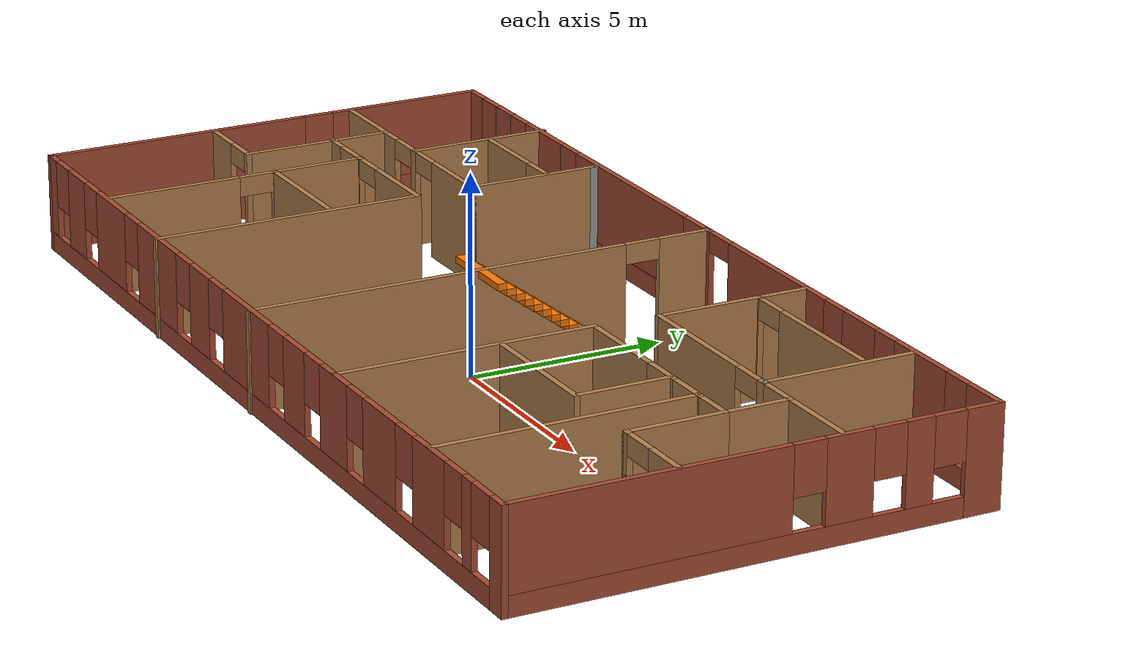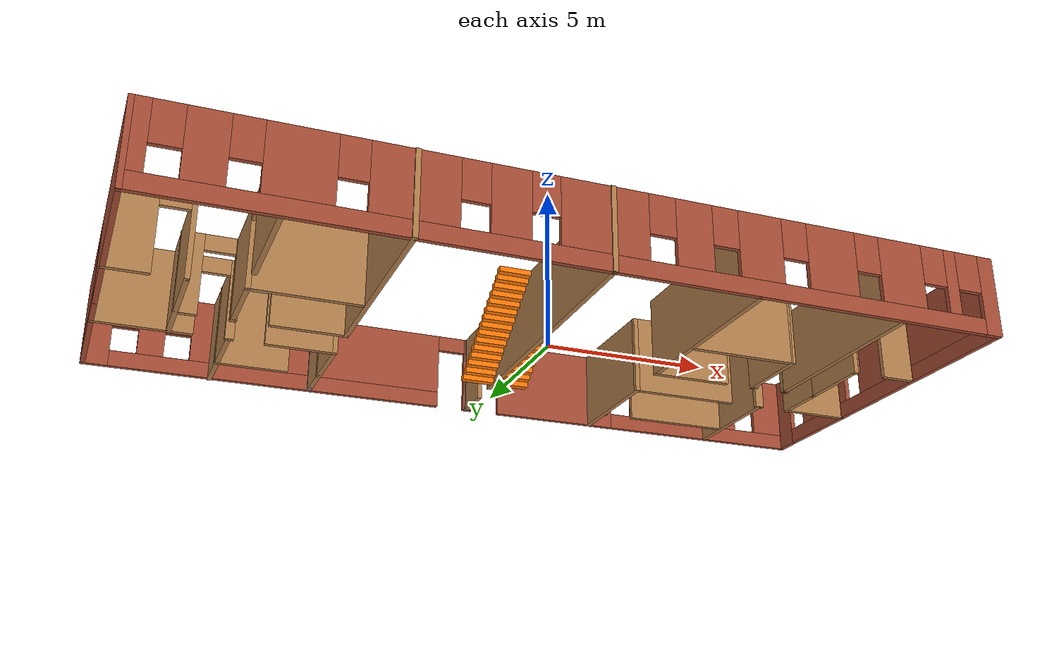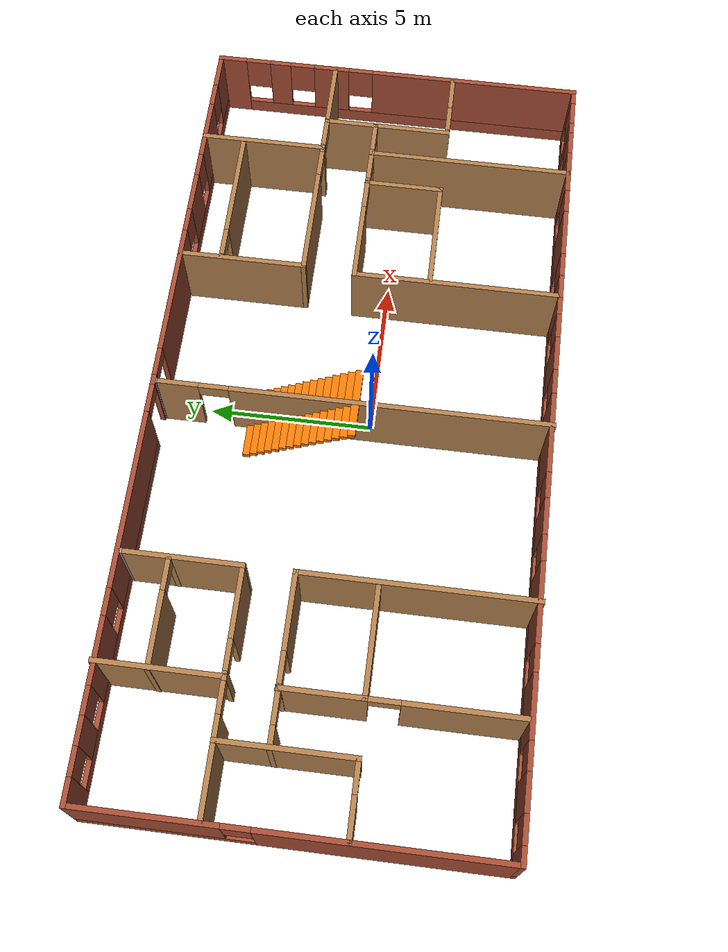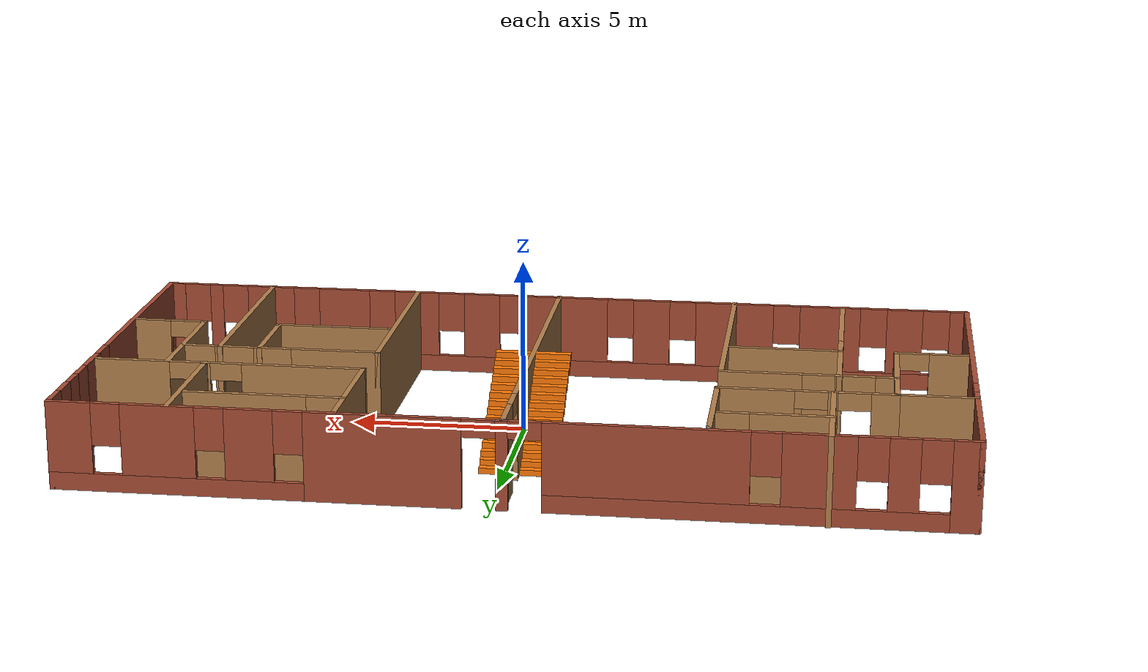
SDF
<?xml version='1.0'?>
<sdf version='1.6'>
  <model name='myhouse'>
    <pose frame=''>-0.386417 0.578117 0 0 -0 0</pose>
    <link name='Stairs_1'>
      <visual name='Stairs_1_Visual_0'>
        <pose frame=''>0.612913 3.12759 0.083333 0 -0 0</pose>
        <geometry>
          <box>
            <size>1 0.233333 0.166667</size>
          </box>
        </geometry>
        <material>
          <script>
            <uri>file://media/materials/scripts/gazebo.material</uri>
            <name>Gazebo/Grey</name>
          </script>
          <ambient>0.996078 0.47451 0.0196078 1</ambient>
        </material>
      </visual>
      <collision name='Stairs_1_Collision_0'>
        <geometry>
          <box>
            <size>1 0.233333 0.166667</size>
          </box>
        </geometry>
        <pose frame=''>0.612913 3.12759 0.083333 0 -0 0</pose>
      </collision>
      <visual name='Stairs_1_Visual_1'>
        <pose frame=''>0.612913 2.89426 0.25 0 -0 0</pose>
        <geometry>
          <box>
            <size>1 0.233333 0.166667</size>
          </box>
        </geometry>
        <material>
          <script>
            <uri>file://media/materials/scripts/gazebo.material</uri>
            <name>Gazebo/Grey</name>
          </script>
          <ambient>0.996078 0.47451 0.0196078 1</ambient>
        </material>
      </visual>
      <collision name='Stairs_1_Collision_1'>
        <geometry>
          <box>
            <size>1 0.233333 0.166667</size>
          </box>
        </geometry>
        <pose frame=''>0.612913 2.89426 0.25 0 -0 0</pose>
      </collision>
      <visual name='Stairs_1_Visual_2'>
        <pose frame=''>0.612913 2.66093 0.416667 0 -0 0</pose>
        <geometry>
          <box>
            <size>1 0.233333 0.166667</size>
          </box>
        </geometry>
        <material>
          <script>
            <uri>file://media/materials/scripts/gazebo.material</uri>
            <name>Gazebo/Grey</name>
          </script>
          <ambient>0.996078 0.47451 0.0196078 1</ambient>
        </material>
      </visual>
      <collision name='Stairs_1_Collision_2'>
        <geometry>
          <box>
            <size>1 0.233333 0.166667</size>
          </box>
        </geometry>
        <pose frame=''>0.612913 2.66093 0.416667 0 -0 0</pose>
      </collision>
      <visual name='Stairs_1_Visual_3'>
        <pose frame=''>0.612913 2.4276 0.583333 0 -0 0</pose>
        <geometry>
          <box>
            <size>1 0.233333 0.166667</size>
          </box>
        </geometry>
        <material>
          <script>
            <uri>file://media/materials/scripts/gazebo.material</uri>
            <name>Gazebo/Grey</name>
          </script>
          <ambient>0.996078 0.47451 0.0196078 1</ambient>
        </material>
      </visual>
      <collision name='Stairs_1_Collision_3'>
        <geometry>
          <box>
            <size>1 0.233333 0.166667</size>
          </box>
        </geometry>
        <pose frame=''>0.612913 2.4276 0.583333 0 -0 0</pose>
      </collision>
      <visual name='Stairs_1_Visual_4'>
        <pose frame=''>0.612913 2.19426 0.75 0 -0 0</pose>
        <geometry>
          <box>
            <size>1 0.233333 0.166667</size>
          </box>
        </geometry>
        <material>
          <script>
            <uri>file://media/materials/scripts/gazebo.material</uri>
            <name>Gazebo/Grey</name>
          </script>
          <ambient>0.996078 0.47451 0.0196078 1</ambient>
        </material>
      </visual>
      <collision name='Stairs_1_Collision_4'>
        <geometry>
          <box>
            <size>1 0.233333 0.166667</size>
          </box>
        </geometry>
        <pose frame=''>0.612913 2.19426 0.75 0 -0 0</pose>
      </collision>
      <visual name='Stairs_1_Visual_5'>
        <pose frame=''>0.612913 1.96093 0.916667 0 -0 0</pose>
        <geometry>
          <box>
            <size>1 0.233333 0.166667</size>
          </box>
        </geometry>
        <material>
          <script>
            <uri>file://media/materials/scripts/gazebo.material</uri>
            <name>Gazebo/Grey</name>
          </script>
          <ambient>0.996078 0.47451 0.0196078 1</ambient>
        </material>
      </visual>
      <collision name='Stairs_1_Collision_5'>
        <geometry>
          <box>
            <size>1 0.233333 0.166667</size>
          </box>
        </geometry>
        <pose frame=''>0.612913 1.96093 0.916667 0 -0 0</pose>
      </collision>
      <visual name='Stairs_1_Visual_6'>
        <pose frame=''>0.612913 1.72759 1.08333 0 -0 0</pose>
        <geometry>
          <box>
            <size>1 0.233333 0.166667</size>
          </box>
        </geometry>
        <material>
          <script>
            <uri>file://media/materials/scripts/gazebo.material</uri>
            <name>Gazebo/Grey</name>
          </script>
          <ambient>0.996078 0.47451 0.0196078 1</ambient>
        </material>
      </visual>
      <collision name='Stairs_1_Collision_6'>
        <geometry>
          <box>
            <size>1 0.233333 0.166667</size>
          </box>
        </geometry>
        <pose frame=''>0.612913 1.72759 1.08333 0 -0 0</pose>
      </collision>
      <visual name='Stairs_1_Visual_7'>
        <pose frame=''>0.612913 1.49426 1.25 0 -0 0</pose>
        <geometry>
          <box>
            <size>1 0.233333 0.166667</size>
          </box>
        </geometry>
        <material>
          <script>
            <uri>file://media/materials/scripts/gazebo.material</uri>
            <name>Gazebo/Grey</name>
          </script>
          <ambient>0.996078 0.47451 0.0196078 1</ambient>
        </material>
      </visual>
      <collision name='Stairs_1_Collision_7'>
        <geometry>
          <box>
            <size>1 0.233333 0.166667</size>
          </box>
        </geometry>
        <pose frame=''>0.612913 1.49426 1.25 0 -0 0</pose>
      </collision>
      <visual name='Stairs_1_Visual_8'>
        <pose frame=''>0.612913 1.26093 1.41667 0 -0 0</pose>
        <geometry>
          <box>
            <size>1 0.233333 0.166667</size>
          </box>
        </geometry>
        <material>
          <script>
            <uri>file://media/materials/scripts/gazebo.material</uri>
            <name>Gazebo/Grey</name>
          </script>
          <ambient>0.996078 0.47451 0.0196078 1</ambient>
        </material>
      </visual>
      <collision name='Stairs_1_Collision_8'>
        <geometry>
          <box>
            <size>1 0.233333 0.166667</size>
          </box>
        </geometry>
        <pose frame=''>0.612913 1.26093 1.41667 0 -0 0</pose>
      </collision>
      <visual name='Stairs_1_Visual_9'>
        <pose frame=''>0.612913 1.0276 1.58333 0 -0 0</pose>
        <geometry>
          <box>
            <size>1 0.233333 0.166667</size>
          </box>
        </geometry>
        <material>
          <script>
            <uri>file://media/materials/scripts/gazebo.material</uri>
            <name>Gazebo/Grey</name>
          </script>
          <ambient>0.996078 0.47451 0.0196078 1</ambient>
        </material>
      </visual>
      <collision name='Stairs_1_Collision_9'>
        <geometry>
          <box>
            <size>1 0.233333 0.166667</size>
          </box>
        </geometry>
        <pose frame=''>0.612913 1.0276 1.58333 0 -0 0</pose>
      </collision>
      <visual name='Stairs_1_Visual_10'>
        <pose frame=''>0.612913 0.794262 1.75 0 -0 0</pose>
        <geometry>
          <box>
            <size>1 0.233333 0.166667</size>
          </box>
        </geometry>
        <material>
          <script>
            <uri>file://media/materials/scripts/gazebo.material</uri>
            <name>Gazebo/Grey</name>
          </script>
          <ambient>0.996078 0.47451 0.0196078 1</ambient>
        </material>
      </visual>
      <collision name='Stairs_1_Collision_10'>
        <geometry>
          <box>
            <size>1 0.233333 0.166667</size>
          </box>
        </geometry>
        <pose frame=''>0.612913 0.794262 1.75 0 -0 0</pose>
      </collision>
      <visual name='Stairs_1_Visual_11'>
        <pose frame=''>0.612913 0.560929 1.91667 0 -0 0</pose>
        <geometry>
          <box>
            <size>1 0.233333 0.166667</size>
          </box>
        </geometry>
        <material>
          <script>
            <uri>file://media/materials/scripts/gazebo.material</uri>
            <name>Gazebo/Grey</name>
          </script>
          <ambient>0.996078 0.47451 0.0196078 1</ambient>
        </material>
      </visual>
      <collision name='Stairs_1_Collision_11'>
        <geometry>
          <box>
            <size>1 0.233333 0.166667</size>
          </box>
        </geometry>
        <pose frame=''>0.612913 0.560929 1.91667 0 -0 0</pose>
      </collision>
      <visual name='Stairs_1_Visual_12'>
        <pose frame=''>0.612913 0.327595 2.08333 0 -0 0</pose>
        <geometry>
          <box>
            <size>1 0.233333 0.166667</size>
          </box>
        </geometry>
        <material>
          <script>
            <uri>file://media/materials/scripts/gazebo.material</uri>
            <name>Gazebo/Grey</name>
          </script>
          <ambient>0.996078 0.47451 0.0196078 1</ambient>
        </material>
      </visual>
      <collision name='Stairs_1_Collision_12'>
        <geometry>
          <box>
            <size>1 0.233333 0.166667</size>
          </box>
        </geometry>
        <pose frame=''>0.612913 0.327595 2.08333 0 -0 0</pose>
      </collision>
      <visual name='Stairs_1_Visual_13'>
        <pose frame=''>0.612913 0.094262 2.25 0 -0 0</pose>
        <geometry>
          <box>
            <size>1 0.233333 0.166667</size>
          </box>
        </geometry>
        <material>
          <script>
            <uri>file://media/materials/scripts/gazebo.material</uri>
            <name>Gazebo/Grey</name>
          </script>
          <ambient>0.996078 0.47451 0.0196078 1</ambient>
        </material>
      </visual>
      <collision name='Stairs_1_Collision_13'>
        <geometry>
          <box>
            <size>1 0.233333 0.166667</size>
          </box>
        </geometry>
        <pose frame=''>0.612913 0.094262 2.25 0 -0 0</pose>
      </collision>
      <visual name='Stairs_1_Visual_14'>
        <pose frame=''>0.612913 -0.139071 2.41667 0 -0 0</pose>
        <geometry>
          <box>
            <size>1 0.233333 0.166667</size>
          </box>
        </geometry>
        <material>
          <script>
            <uri>file://media/materials/scripts/gazebo.material</uri>
            <name>Gazebo/Grey</name>
          </script>
          <ambient>0.996078 0.47451 0.0196078 1</ambient>
        </material>
      </visual>
      <collision name='Stairs_1_Collision_14'>
        <geometry>
          <box>
            <size>1 0.233333 0.166667</size>
          </box>
        </geometry>
        <pose frame=''>0.612913 -0.139071 2.41667 0 -0 0</pose>
      </collision>
    </link>
    <link name='Stairs_2'>
      <visual name='Stairs_2_Visual_0'>
        <pose frame=''>-0.53356 3.12759 0.083333 0 -0 0</pose>
        <geometry>
          <box>
            <size>1 0.233333 0.166667</size>
          </box>
        </geometry>
        <material>
          <script>
            <uri>file://media/materials/scripts/gazebo.material</uri>
            <name>Gazebo/Grey</name>
          </script>
          <ambient>0.996078 0.47451 0.0196078 1</ambient>
        </material>
      </visual>
      <collision name='Stairs_2_Collision_0'>
        <geometry>
          <box>
            <size>1 0.233333 0.166667</size>
          </box>
        </geometry>
        <pose frame=''>-0.53356 3.12759 0.083333 0 -0 0</pose>
      </collision>
      <visual name='Stairs_2_Visual_1'>
        <pose frame=''>-0.53356 2.89426 0.25 0 -0 0</pose>
        <geometry>
          <box>
            <size>1 0.233333 0.166667</size>
          </box>
        </geometry>
        <material>
          <script>
            <uri>file://media/materials/scripts/gazebo.material</uri>
            <name>Gazebo/Grey</name>
          </script>
          <ambient>0.996078 0.47451 0.0196078 1</ambient>
        </material>
      </visual>
      <collision name='Stairs_2_Collision_1'>
        <geometry>
          <box>
            <size>1 0.233333 0.166667</size>
          </box>
        </geometry>
        <pose frame=''>-0.53356 2.89426 0.25 0 -0 0</pose>
      </collision>
      <visual name='Stairs_2_Visual_2'>
        <pose frame=''>-0.53356 2.66093 0.416667 0 -0 0</pose>
        <geometry>
          <box>
            <size>1 0.233333 0.166667</size>
          </box>
        </geometry>
        <material>
          <script>
            <uri>file://media/materials/scripts/gazebo.material</uri>
            <name>Gazebo/Grey</name>
          </script>
          <ambient>0.996078 0.47451 0.0196078 1</ambient>
        </material>
      </visual>
      <collision name='Stairs_2_Collision_2'>
        <geometry>
          <box>
            <size>1 0.233333 0.166667</size>
          </box>
        </geometry>
        <pose frame=''>-0.53356 2.66093 0.416667 0 -0 0</pose>
      </collision>
      <visual name='Stairs_2_Visual_3'>
        <pose frame=''>-0.53356 2.4276 0.583333 0 -0 0</pose>
        <geometry>
          <box>
            <size>1 0.233333 0.166667</size>
          </box>
        </geometry>
        <material>
          <script>
            <uri>file://media/materials/scripts/gazebo.material</uri>
            <name>Gazebo/Grey</name>
          </script>
          <ambient>0.996078 0.47451 0.0196078 1</ambient>
        </material>
      </visual>
      <collision name='Stairs_2_Collision_3'>
        <geometry>
          <box>
            <size>1 0.233333 0.166667</size>
          </box>
        </geometry>
        <pose frame=''>-0.53356 2.4276 0.583333 0 -0 0</pose>
      </collision>
      <visual name='Stairs_2_Visual_4'>
        <pose frame=''>-0.53356 2.19426 0.75 0 -0 0</pose>
        <geometry>
          <box>
            <size>1 0.233333 0.166667</size>
          </box>
        </geometry>
        <material>
          <script>
            <uri>file://media/materials/scripts/gazebo.material</uri>
            <name>Gazebo/Grey</name>
          </script>
          <ambient>0.996078 0.47451 0.0196078 1</ambient>
        </material>
      </visual>
      <collision name='Stairs_2_Collision_4'>
        <geometry>
          <box>
            <size>1 0.233333 0.166667</size>
          </box>
        </geometry>
        <pose frame=''>-0.53356 2.19426 0.75 0 -0 0</pose>
      </collision>
      <visual name='Stairs_2_Visual_5'>
        <pose frame=''>-0.53356 1.96093 0.916667 0 -0 0</pose>
        <geometry>
          <box>
            <size>1 0.233333 0.166667</size>
          </box>
        </geometry>
        <material>
          <script>
            <uri>file://media/materials/scripts/gazebo.material</uri>
            <name>Gazebo/Grey</name>
          </script>
          <ambient>0.996078 0.47451 0.0196078 1</ambient>
        </material>
      </visual>
      <collision name='Stairs_2_Collision_5'>
        <geometry>
          <box>
            <size>1 0.233333 0.166667</size>
          </box>
        </geometry>
        <pose frame=''>-0.53356 1.96093 0.916667 0 -0 0</pose>
      </collision>
      <visual name='Stairs_2_Visual_6'>
        <pose frame=''>-0.53356 1.72759 1.08333 0 -0 0</pose>
        <geometry>
          <box>
            <size>1 0.233333 0.166667</size>
          </box>
        </geometry>
        <material>
          <script>
            <uri>file://media/materials/scripts/gazebo.material</uri>
            <name>Gazebo/Grey</name>
          </script>
          <ambient>0.996078 0.47451 0.0196078 1</ambient>
        </material>
      </visual>
      <collision name='Stairs_2_Collision_6'>
        <geometry>
          <box>
            <size>1 0.233333 0.166667</size>
          </box>
        </geometry>
        <pose frame=''>-0.53356 1.72759 1.08333 0 -0 0</pose>
      </collision>
      <visual name='Stairs_2_Visual_7'>
        <pose frame=''>-0.53356 1.49426 1.25 0 -0 0</pose>
        <geometry>
          <box>
            <size>1 0.233333 0.166667</size>
          </box>
        </geometry>
        <material>
          <script>
            <uri>file://media/materials/scripts/gazebo.material</uri>
            <name>Gazebo/Grey</name>
          </script>
          <ambient>0.996078 0.47451 0.0196078 1</ambient>
        </material>
      </visual>
      <collision name='Stairs_2_Collision_7'>
        <geometry>
          <box>
            <size>1 0.233333 0.166667</size>
          </box>
        </geometry>
        <pose frame=''>-0.53356 1.49426 1.25 0 -0 0</pose>
      </collision>
      <visual name='Stairs_2_Visual_8'>
        <pose frame=''>-0.53356 1.26093 1.41667 0 -0 0</pose>
        <geometry>
          <box>
            <size>1 0.233333 0.166667</size>
          </box>
        </geometry>
        <material>
          <script>
            <uri>file://media/materials/scripts/gazebo.material</uri>
            <name>Gazebo/Grey</name>
          </script>
          <ambient>0.996078 0.47451 0.0196078 1</ambient>
        </material>
      </visual>
      <collision name='Stairs_2_Collision_8'>
        <geometry>
          <box>
            <size>1 0.233333 0.166667</size>
          </box>
        </geometry>
        <pose frame=''>-0.53356 1.26093 1.41667 0 -0 0</pose>
      </collision>
      <visual name='Stairs_2_Visual_9'>
        <pose frame=''>-0.53356 1.0276 1.58333 0 -0 0</pose>
        <geometry>
          <box>
            <size>1 0.233333 0.166667</size>
          </box>
        </geometry>
        <material>
          <script>
            <uri>file://media/materials/scripts/gazebo.material</uri>
            <name>Gazebo/Grey</name>
          </script>
          <ambient>0.996078 0.47451 0.0196078 1</ambient>
        </material>
      </visual>
      <collision name='Stairs_2_Collision_9'>
        <geometry>
          <box>
            <size>1 0.233333 0.166667</size>
          </box>
        </geometry>
        <pose frame=''>-0.53356 1.0276 1.58333 0 -0 0</pose>
      </collision>
      <visual name='Stairs_2_Visual_10'>
        <pose frame=''>-0.53356 0.794262 1.75 0 -0 0</pose>
        <geometry>
          <box>
            <size>1 0.233333 0.166667</size>
          </box>
        </geometry>
        <material>
          <script>
            <uri>file://media/materials/scripts/gazebo.material</uri>
            <name>Gazebo/Grey</name>
          </script>
          <ambient>0.996078 0.47451 0.0196078 1</ambient>
        </material>
      </visual>
      <collision name='Stairs_2_Collision_10'>
        <geometry>
          <box>
            <size>1 0.233333 0.166667</size>
          </box>
        </geometry>
        <pose frame=''>-0.53356 0.794262 1.75 0 -0 0</pose>
      </collision>
      <visual name='Stairs_2_Visual_11'>
        <pose frame=''>-0.53356 0.560929 1.91667 0 -0 0</pose>
        <geometry>
          <box>
            <size>1 0.233333 0.166667</size>
          </box>
        </geometry>
        <material>
          <script>
            <uri>file://media/materials/scripts/gazebo.material</uri>
            <name>Gazebo/Grey</name>
          </script>
          <ambient>0.996078 0.47451 0.0196078 1</ambient>
        </material>
      </visual>
      <collision name='Stairs_2_Collision_11'>
        <geometry>
          <box>
            <size>1 0.233333 0.166667</size>
          </box>
        </geometry>
        <pose frame=''>-0.53356 0.560929 1.91667 0 -0 0</pose>
      </collision>
      <visual name='Stairs_2_Visual_12'>
        <pose frame=''>-0.53356 0.327595 2.08333 0 -0 0</pose>
        <geometry>
          <box>
            <size>1 0.233333 0.166667</size>
          </box>
        </geometry>
        <material>
          <script>
            <uri>file://media/materials/scripts/gazebo.material</uri>
            <name>Gazebo/Grey</name>
          </script>
          <ambient>0.996078 0.47451 0.0196078 1</ambient>
        </material>
      </visual>
      <collision name='Stairs_2_Collision_12'>
        <geometry>
          <box>
            <size>1 0.233333 0.166667</size>
          </box>
        </geometry>
        <pose frame=''>-0.53356 0.327595 2.08333 0 -0 0</pose>
      </collision>
      <visual name='Stairs_2_Visual_13'>
        <pose frame=''>-0.53356 0.094262 2.25 0 -0 0</pose>
        <geometry>
          <box>
            <size>1 0.233333 0.166667</size>
          </box>
        </geometry>
        <material>
          <script>
            <uri>file://media/materials/scripts/gazebo.material</uri>
            <name>Gazebo/Grey</name>
          </script>
          <ambient>0.996078 0.47451 0.0196078 1</ambient>
        </material>
      </visual>
      <collision name='Stairs_2_Collision_13'>
        <geometry>
          <box>
            <size>1 0.233333 0.166667</size>
          </box>
        </geometry>
        <pose frame=''>-0.53356 0.094262 2.25 0 -0 0</pose>
      </collision>
      <visual name='Stairs_2_Visual_14'>
        <pose frame=''>-0.53356 -0.139071 2.41667 0 -0 0</pose>
        <geometry>
          <box>
            <size>1 0.233333 0.166667</size>
          </box>
        </geometry>
        <material>
          <script>
            <uri>file://media/materials/scripts/gazebo.material</uri>
            <name>Gazebo/Grey</name>
          </script>
          <ambient>0.996078 0.47451 0.0196078 1</ambient>
        </material>
      </visual>
      <collision name='Stairs_2_Collision_14'>
        <geometry>
          <box>
            <size>1 0.233333 0.166667</size>
          </box>
        </geometry>
        <pose frame=''>-0.53356 -0.139071 2.41667 0 -0 0</pose>
      </collision>
    </link>
    <link name='Wall_10'>
      <pose frame=''>-12.3 -0.005752 0 0 -0 1.5708</pose>
      <visual name='Wall_10_Visual_0'>
        <pose frame=''>-2.48016 0 1.25 0 -0 0</pose>
        <geometry>
          <box>
            <size>7.03967 0.15 2.5</size>
          </box>
        </geometry>
        <material>
          <script>
            <uri>file://media/materials/scripts/gazebo.material</uri>
            <name>Gazebo/Bricks</name>
          </script>
          <ambient>0.435294 0.796078 0.67451 1</ambient>
        </material>
      </visual>
      <collision name='Wall_10_Collision_0'>
        <geometry>
          <box>
            <size>7.03967 0.15 2.5</size>
          </box>
        </geometry>
        <pose frame=''>-2.48016 0 1.25 0 -0 0</pose>
      </collision>
      <visual name='Wall_10_Visual_1'>
        <pose frame=''>3.51984 0 0.25 0 -0 0</pose>
        <geometry>
          <box>
            <size>4.96033 0.15 0.5</size>
          </box>
        </geometry>
        <material>
          <script>
            <uri>file://media/materials/scripts/gazebo.material</uri>
            <name>Gazebo/Bricks</name>
          </script>
          <ambient>0.435294 0.796078 0.67451 1</ambient>
        </material>
      </visual>
      <collision name='Wall_10_Collision_1'>
        <geometry>
          <box>
            <size>4.96033 0.15 0.5</size>
          </box>
        </geometry>
        <pose frame=''>3.51984 0 0.25 0 -0 0</pose>
      </collision>
      <visual name='Wall_10_Visual_2'>
        <pose frame=''>3.91984 0 1.5 0 -0 0</pose>
        <geometry>
          <box>
            <size>4.16033 0.15 2</size>
          </box>
        </geometry>
        <material>
          <script>
            <uri>file://media/materials/scripts/gazebo.material</uri>
            <name>Gazebo/Bricks</name>
          </script>
          <ambient>0.435294 0.796078 0.67451 1</ambient>
        </material>
      </visual>
      <collision name='Wall_10_Collision_2'>
        <geometry>
          <box>
            <size>4.16033 0.15 2</size>
          </box>
        </geometry>
        <pose frame=''>3.91984 0 1.5 0 -0 0</pose>
      </collision>
      <visual name='Wall_10_Visual_3'>
        <pose frame=''>1.43967 0 1.9 0 -0 0</pose>
        <geometry>
          <box>
            <size>0.8 0.15 1.2</size>
          </box>
        </geometry>
        <material>
          <script>
            <uri>file://media/materials/scripts/gazebo.material</uri>
            <name>Gazebo/Bricks</name>
          </script>
          <ambient>0.435294 0.796078 0.67451 1</ambient>
        </material>
      </visual>
      <collision name='Wall_10_Collision_3'>
        <geometry>
          <box>
            <size>0.8 0.15 1.2</size>
          </box>
        </geometry>
        <pose frame=''>1.43967 0 1.9 0 -0 0</pose>
      </collision>
    </link>
    <link name='Wall_14'>
      <collision name='Wall_14_Collision'>
        <geometry>
          <box>
            <size>0.16 0.15 2.5</size>
          </box>
        </geometry>
        <pose frame=''>0 0 1.25 0 -0 0</pose>
      </collision>
      <visual name='Wall_14_Visual'>
        <pose frame=''>0 0 1.25 0 -0 0</pose>
        <geometry>
          <box>
            <size>0.16 0.15 2.5</size>
          </box>
        </geometry>
        <material>
          <script>
            <uri>file://media/materials/scripts/gazebo.material</uri>
            <name>Gazebo/Grey</name>
          </script>
          <ambient>1 1 1 1</ambient>
        </material>
      </visual>
      <pose frame=''>0.03462 5.87902 0 0 -0 0</pose>
    </link>
    <link name='Wall_15'>
      <pose frame=''>0.03962 -0.045979 0 0 0 -1.5708</pose>
      <visual name='Wall_15_Visual_0'>
        <pose frame=''>-5.3025 0 1.25 0 -0 0</pose>
        <geometry>
          <box>
            <size>1.39499 0.15 2.5</size>
          </box>
        </geometry>
        <material>
          <script>
            <uri>file://media/materials/scripts/gazebo.material</uri>
            <name>Gazebo/Wood</name>
          </script>
          <ambient>1 1 1 1</ambient>
        </material>
      </visual>
      <collision name='Wall_15_Collision_0'>
        <geometry>
          <box>
            <size>1.39499 0.15 2.5</size>
          </box>
        </geometry>
        <pose frame=''>-5.3025 0 1.25 0 -0 0</pose>
      </collision>
      <visual name='Wall_15_Visual_1'>
        <pose frame=''>1.1475 0 1.25 0 -0 0</pose>
        <geometry>
          <box>
            <size>9.70501 0.15 2.5</size>
          </box>
        </geometry>
        <material>
          <script>
            <uri>file://media/materials/scripts/gazebo.material</uri>
            <name>Gazebo/Wood</name>
          </script>
          <ambient>1 1 1 1</ambient>
        </material>
      </visual>
      <collision name='Wall_15_Collision_1'>
        <geometry>
          <box>
            <size>9.70501 0.15 2.5</size>
          </box>
        </geometry>
        <pose frame=''>1.1475 0 1.25 0 -0 0</pose>
      </collision>
      <visual name='Wall_15_Visual_2'>
        <pose frame=''>-4.15501 0 2.25 0 -0 0</pose>
        <geometry>
          <box>
            <size>0.9 0.15 0.5</size>
          </box>
        </geometry>
        <material>
          <script>
            <uri>file://media/materials/scripts/gazebo.material</uri>
            <name>Gazebo/Wood</name>
          </script>
          <ambient>1 1 1 1</ambient>
        </material>
      </visual>
      <collision name='Wall_15_Collision_2'>
        <geometry>
          <box>
            <size>0.9 0.15 0.5</size>
          </box>
        </geometry>
        <pose frame=''>-4.15501 0 2.25 0 -0 0</pose>
      </collision>
    </link>
    <link name='Wall_17'>
      <collision name='Wall_17_Collision'>
        <geometry>
          <box>
            <size>6.5 0.15 2.5</size>
          </box>
        </geometry>
        <pose frame=''>0 0 1.25 0 -0 0</pose>
      </collision>
      <visual name='Wall_17_Visual'>
        <pose frame=''>0 0 1.25 0 -0 0</pose>
        <geometry>
          <box>
            <size>6.5 0.15 2.5</size>
          </box>
        </geometry>
        <material>
          <script>
            <uri>file://media/materials/scripts/gazebo.material</uri>
            <name>Gazebo/Wood</name>
          </script>
          <ambient>1 1 1 1</ambient>
        </material>
      </visual>
      <pose frame=''>4.43449 -2.73253 0 0 -0 1.5708</pose>
    </link>
    <link name='Wall_18'>
      <pose frame=''>6.73449 0.442468 0 0 -0 0</pose>
      <visual name='Wall_18_Visual_0'>
        <pose frame=''>-1.08415 0 1.25 0 -0 0</pose>
        <geometry>
          <box>
            <size>2.58169 0.15 2.5</size>
          </box>
        </geometry>
        <material>
          <script>
            <uri>file://media/materials/scripts/gazebo.material</uri>
            <name>Gazebo/Wood</name>
          </script>
          <ambient>1 1 1 1</ambient>
        </material>
      </visual>
      <collision name='Wall_18_Collision_0'>
        <geometry>
          <box>
            <size>2.58169 0.15 2.5</size>
          </box>
        </geometry>
        <pose frame=''>-1.08415 0 1.25 0 -0 0</pose>
      </collision>
      <visual name='Wall_18_Visual_1'>
        <pose frame=''>1.20982 0 1.25 0 -0 0</pose>
        <geometry>
          <box>
            <size>0.206246 0.15 2.5</size>
          </box>
        </geometry>
        <material>
          <script>
            <uri>file://media/materials/scripts/gazebo.material</uri>
            <name>Gazebo/Wood</name>
          </script>
          <ambient>1 1 1 1</ambient>
        </material>
      </visual>
      <collision name='Wall_18_Collision_1'>
        <geometry>
          <box>
            <size>0.206246 0.15 2.5</size>
          </box>
        </geometry>
        <pose frame=''>1.20982 0 1.25 0 -0 0</pose>
      </collision>
      <visual name='Wall_18_Visual_2'>
        <pose frame=''>2.29397 0 1.25 0 -0 0</pose>
        <geometry>
          <box>
            <size>0.162059 0.15 2.5</size>
          </box>
        </geometry>
        <material>
          <script>
            <uri>file://media/materials/scripts/gazebo.material</uri>
            <name>Gazebo/Wood</name>
          </script>
          <ambient>1 1 1 1</ambient>
        </material>
      </visual>
      <collision name='Wall_18_Collision_2'>
        <geometry>
          <box>
            <size>0.162059 0.15 2.5</size>
          </box>
        </geometry>
        <pose frame=''>2.29397 0 1.25 0 -0 0</pose>
      </collision>
      <visual name='Wall_18_Visual_3'>
        <pose frame=''>0.656695 0 2.25 0 -0 0</pose>
        <geometry>
          <box>
            <size>0.9 0.15 0.5</size>
          </box>
        </geometry>
        <material>
          <script>
            <uri>file://media/materials/scripts/gazebo.material</uri>
            <name>Gazebo/Wood</name>
          </script>
          <ambient>1 1 1 1</ambient>
        </material>
      </visual>
      <collision name='Wall_18_Collision_3'>
        <geometry>
          <box>
            <size>0.9 0.15 0.5</size>
          </box>
        </geometry>
        <pose frame=''>0.656695 0 2.25 0 -0 0</pose>
      </collision>
      <visual name='Wall_18_Visual_4'>
        <pose frame=''>1.76294 0 2.25 0 -0 0</pose>
        <geometry>
          <box>
            <size>0.9 0.15 0.5</size>
          </box>
        </geometry>
        <material>
          <script>
            <uri>file://media/materials/scripts/gazebo.material</uri>
            <name>Gazebo/Wood</name>
          </script>
          <ambient>1 1 1 1</ambient>
        </material>
      </visual>
      <collision name='Wall_18_Collision_4'>
        <geometry>
          <box>
            <size>0.9 0.15 0.5</size>
          </box>
        </geometry>
        <pose frame=''>1.76294 0 2.25 0 -0 0</pose>
      </collision>
    </link>
    <link name='Wall_19'>
      <collision name='Wall_19_Collision'>
        <geometry>
          <box>
            <size>6.5 0.15 2.5</size>
          </box>
        </geometry>
        <pose frame=''>0 0 1.25 0 -0 0</pose>
      </collision>
      <visual name='Wall_19_Visual'>
        <pose frame=''>0 0 1.25 0 -0 0</pose>
        <geometry>
          <box>
            <size>6.5 0.15 2.5</size>
          </box>
        </geometry>
        <material>
          <script>
            <uri>file://media/materials/scripts/gazebo.material</uri>
            <name>Gazebo/Wood</name>
          </script>
          <ambient>1 1 1 1</ambient>
        </material>
      </visual>
      <pose frame=''>9.03449 -2.73253 0 0 0 -1.5708</pose>
    </link>
    <link name='Wall_21'>
      <collision name='Wall_21_Collision'>
        <geometry>
          <box>
            <size>2.5 0.15 2.5</size>
          </box>
        </geometry>
        <pose frame=''>0 0 1.25 0 -0 0</pose>
      </collision>
      <visual name='Wall_21_Visual'>
        <pose frame=''>0 0 1.25 0 -0 0</pose>
        <geometry>
          <box>
            <size>2.5 0.15 2.5</size>
          </box>
        </geometry>
        <material>
          <script>
            <uri>file://media/materials/scripts/gazebo.material</uri>
            <name>Gazebo/Wood</name>
          </script>
          <ambient>1 1 1 1</ambient>
        </material>
      </visual>
      <pose frame=''>7.87391 -0.726644 0 0 0 -1.5708</pose>
    </link>
    <link name='Wall_22'>
      <collision name='Wall_22_Collision'>
        <geometry>
          <box>
            <size>3.5 0.15 2.5</size>
          </box>
        </geometry>
        <pose frame=''>0 0 1.25 0 -0 0</pose>
      </collision>
      <visual name='Wall_22_Visual'>
        <pose frame=''>0 0 1.25 0 -0 0</pose>
        <geometry>
          <box>
            <size>3.5 0.15 2.5</size>
          </box>
        </geometry>
        <material>
          <script>
            <uri>file://media/materials/scripts/gazebo.material</uri>
            <name>Gazebo/Wood</name>
          </script>
          <ambient>1 1 1 1</ambient>
        </material>
      </visual>
      <pose frame=''>6.19891 -1.90164 0 0 -0 3.14159</pose>
    </link>
    <link name='Wall_24'>
      <pose frame=''>9.58449 0.442468 0 0 -0 0</pose>
      <visual name='Wall_24_Visual_0'>
        <pose frame=''>-0.51785 0 1.25 0 -0 0</pose>
        <geometry>
          <box>
            <size>0.214301 0.15 2.5</size>
          </box>
        </geometry>
        <material>
          <script>
            <uri>file://media/materials/scripts/gazebo.material</uri>
            <name>Gazebo/Wood</name>
          </script>
          <ambient>1 1 1 1</ambient>
        </material>
      </visual>
      <collision name='Wall_24_Collision_0'>
        <geometry>
          <box>
            <size>0.214301 0.15 2.5</size>
          </box>
        </geometry>
        <pose frame=''>-0.51785 0 1.25 0 -0 0</pose>
      </collision>
      <visual name='Wall_24_Visual_1'>
        <pose frame=''>0.55715 0 1.25 0 -0 0</pose>
        <geometry>
          <box>
            <size>0.135699 0.15 2.5</size>
          </box>
        </geometry>
        <material>
          <script>
            <uri>file://media/materials/scripts/gazebo.material</uri>
            <name>Gazebo/Wood</name>
          </script>
          <ambient>1 1 1 1</ambient>
        </material>
      </visual>
      <collision name='Wall_24_Collision_1'>
        <geometry>
          <box>
            <size>0.135699 0.15 2.5</size>
          </box>
        </geometry>
        <pose frame=''>0.55715 0 1.25 0 -0 0</pose>
      </collision>
      <visual name='Wall_24_Visual_2'>
        <pose frame=''>0.039301 0 2.25 0 -0 0</pose>
        <geometry>
          <box>
            <size>0.9 0.15 0.5</size>
          </box>
        </geometry>
        <material>
          <script>
            <uri>file://media/materials/scripts/gazebo.material</uri>
            <name>Gazebo/Wood</name>
          </script>
          <ambient>1 1 1 1</ambient>
        </material>
      </visual>
      <collision name='Wall_24_Collision_2'>
        <geometry>
          <box>
            <size>0.9 0.15 0.5</size>
          </box>
        </geometry>
        <pose frame=''>0.039301 0 2.25 0 -0 0</pose>
      </collision>
    </link>
    <link name='Wall_25'>
      <collision name='Wall_25_Collision'>
        <geometry>
          <box>
            <size>1.75 0.15 2.5</size>
          </box>
        </geometry>
        <pose frame=''>0 0 1.25 0 -0 0</pose>
      </collision>
      <visual name='Wall_25_Visual'>
        <pose frame=''>0 0 1.25 0 -0 0</pose>
        <geometry>
          <box>
            <size>1.75 0.15 2.5</size>
          </box>
        </geometry>
        <material>
          <script>
            <uri>file://media/materials/scripts/gazebo.material</uri>
            <name>Gazebo/Wood</name>
          </script>
          <ambient>1 1 1 1</ambient>
        </material>
      </visual>
      <pose frame=''>10.1345 1.24247 0 0 -0 1.5708</pose>
    </link>
    <link name='Wall_26'>
      <collision name='Wall_26_Collision'>
        <geometry>
          <box>
            <size>2.25 0.15 2.5</size>
          </box>
        </geometry>
        <pose frame=''>0 0 1.25 0 -0 0</pose>
      </collision>
      <visual name='Wall_26_Visual'>
        <pose frame=''>0 0 1.25 0 -0 0</pose>
        <geometry>
          <box>
            <size>2.25 0.15 2.5</size>
          </box>
        </geometry>
        <material>
          <script>
            <uri>file://media/materials/scripts/gazebo.material</uri>
            <name>Gazebo/Wood</name>
          </script>
          <ambient>1 1 1 1</ambient>
        </material>
      </visual>
      <pose frame=''>11.1845 2.04247 0 0 -0 0</pose>
    </link>
    <link name='Wall_28'>
      <collision name='Wall_28_Collision'>
        <geometry>
          <box>
            <size>2.5 0.15 2.5</size>
          </box>
        </geometry>
        <pose frame=''>0 0 1.25 0 -0 0</pose>
      </collision>
      <visual name='Wall_28_Visual'>
        <pose frame=''>0 0 1.25 0 -0 0</pose>
        <geometry>
          <box>
            <size>2.5 0.15 2.5</size>
          </box>
        </geometry>
        <material>
          <script>
            <uri>file://media/materials/scripts/gazebo.material</uri>
            <name>Gazebo/Wood</name>
          </script>
          <ambient>1 1 1 1</ambient>
        </material>
      </visual>
      <pose frame=''>10.1345 -0.732532 0 0 0 -1.5708</pose>
    </link>
    <link name='Wall_29'>
      <pose frame=''>11.1845 -1.90753 0 0 -0 0</pose>
      <visual name='Wall_29_Visual_0'>
        <pose frame=''>-1.02478 0 1.25 0 -0 0</pose>
        <geometry>
          <box>
            <size>0.200434 0.15 2.5</size>
          </box>
        </geometry>
        <material>
          <script>
            <uri>file://media/materials/scripts/gazebo.material</uri>
            <name>Gazebo/Wood</name>
          </script>
          <ambient>1 1 1 1</ambient>
        </material>
      </visual>
      <collision name='Wall_29_Collision_0'>
        <geometry>
          <box>
            <size>0.200434 0.15 2.5</size>
          </box>
        </geometry>
        <pose frame=''>-1.02478 0 1.25 0 -0 0</pose>
      </collision>
      <visual name='Wall_29_Visual_1'>
        <pose frame=''>0.550217 0 1.25 0 -0 0</pose>
        <geometry>
          <box>
            <size>1.14957 0.15 2.5</size>
          </box>
        </geometry>
        <material>
          <script>
            <uri>file://media/materials/scripts/gazebo.material</uri>
            <name>Gazebo/Wood</name>
          </script>
          <ambient>1 1 1 1</ambient>
        </material>
      </visual>
      <collision name='Wall_29_Collision_1'>
        <geometry>
          <box>
            <size>1.14957 0.15 2.5</size>
          </box>
        </geometry>
        <pose frame=''>0.550217 0 1.25 0 -0 0</pose>
      </collision>
      <visual name='Wall_29_Visual_2'>
        <pose frame=''>-0.474566 0 2.25 0 -0 0</pose>
        <geometry>
          <box>
            <size>0.9 0.15 0.5</size>
          </box>
        </geometry>
        <material>
          <script>
            <uri>file://media/materials/scripts/gazebo.material</uri>
            <name>Gazebo/Wood</name>
          </script>
          <ambient>1 1 1 1</ambient>
        </material>
      </visual>
      <collision name='Wall_29_Collision_2'>
        <geometry>
          <box>
            <size>0.9 0.15 0.5</size>
          </box>
        </geometry>
        <pose frame=''>-0.474566 0 2.25 0 -0 0</pose>
      </collision>
    </link>
    <link name='Wall_31'>
      <pose frame=''>7.33449 2.04247 0 0 -0 3.14159</pose>
      <visual name='Wall_31_Visual_0'>
        <pose frame=''>-2.80715 0 1.25 0 -0 0</pose>
        <geometry>
          <box>
            <size>0.135699 0.15 2.5</size>
          </box>
        </geometry>
        <material>
          <script>
            <uri>file://media/materials/scripts/gazebo.material</uri>
            <name>Gazebo/Wood</name>
          </script>
          <ambient>1 1 1 1</ambient>
        </material>
      </visual>
      <collision name='Wall_31_Collision_0'>
        <geometry>
          <box>
            <size>0.135699 0.15 2.5</size>
          </box>
        </geometry>
        <pose frame=''>-2.80715 0 1.25 0 -0 0</pose>
      </collision>
      <visual name='Wall_31_Visual_1'>
        <pose frame=''>-1.69595 0 1.25 0 -0 0</pose>
        <geometry>
          <box>
            <size>0.286701 0.15 2.5</size>
          </box>
        </geometry>
        <material>
          <script>
            <uri>file://media/materials/scripts/gazebo.material</uri>
            <name>Gazebo/Wood</name>
          </script>
          <ambient>1 1 1 1</ambient>
        </material>
      </visual>
      <collision name='Wall_31_Collision_1'>
        <geometry>
          <box>
            <size>0.286701 0.15 2.5</size>
          </box>
        </geometry>
        <pose frame=''>-1.69595 0 1.25 0 -0 0</pose>
      </collision>
      <visual name='Wall_31_Visual_2'>
        <pose frame=''>1.1112 0 1.25 0 -0 0</pose>
        <geometry>
          <box>
            <size>3.5276 0.15 2.5</size>
          </box>
        </geometry>
        <material>
          <script>
            <uri>file://media/materials/scripts/gazebo.material</uri>
            <name>Gazebo/Wood</name>
          </script>
          <ambient>1 1 1 1</ambient>
        </material>
      </visual>
      <collision name='Wall_31_Collision_2'>
        <geometry>
          <box>
            <size>3.5276 0.15 2.5</size>
          </box>
        </geometry>
        <pose frame=''>1.1112 0 1.25 0 -0 0</pose>
      </collision>
      <visual name='Wall_31_Visual_3'>
        <pose frame=''>-2.2893 0 2.25 0 -0 0</pose>
        <geometry>
          <box>
            <size>0.9 0.15 0.5</size>
          </box>
        </geometry>
        <material>
          <script>
            <uri>file://media/materials/scripts/gazebo.material</uri>
            <name>Gazebo/Wood</name>
          </script>
          <ambient>1 1 1 1</ambient>
        </material>
      </visual>
      <collision name='Wall_31_Collision_3'>
        <geometry>
          <box>
            <size>0.9 0.15 0.5</size>
          </box>
        </geometry>
        <pose frame=''>-2.2893 0 2.25 0 -0 0</pose>
      </collision>
      <visual name='Wall_31_Visual_4'>
        <pose frame=''>-1.1026 0 2.25 0 -0 0</pose>
        <geometry>
          <box>
            <size>0.9 0.15 0.5</size>
          </box>
        </geometry>
        <material>
          <script>
            <uri>file://media/materials/scripts/gazebo.material</uri>
            <name>Gazebo/Wood</name>
          </script>
          <ambient>1 1 1 1</ambient>
        </material>
      </visual>
      <collision name='Wall_31_Collision_4'>
        <geometry>
          <box>
            <size>0.9 0.15 0.5</size>
          </box>
        </geometry>
        <pose frame=''>-1.1026 0 2.25 0 -0 0</pose>
      </collision>
    </link>
    <link name='Wall_32'>
      <collision name='Wall_32_Collision'>
        <geometry>
          <box>
            <size>4 0.15 2.5</size>
          </box>
        </geometry>
        <pose frame=''>0 0 1.25 0 -0 0</pose>
      </collision>
      <visual name='Wall_32_Visual'>
        <pose frame=''>0 0 1.25 0 -0 0</pose>
        <geometry>
          <box>
            <size>4 0.15 2.5</size>
          </box>
        </geometry>
        <material>
          <script>
            <uri>file://media/materials/scripts/gazebo.material</uri>
            <name>Gazebo/Wood</name>
          </script>
          <ambient>1 1 1 1</ambient>
        </material>
      </visual>
      <pose frame=''>4.53449 3.96747 0 0 -0 1.5708</pose>
    </link>
    <link name='Wall_34'>
      <collision name='Wall_34_Collision'>
        <geometry>
          <box>
            <size>0.16 0.15 2.5</size>
          </box>
        </geometry>
        <pose frame=''>0 0 1.25 0 -0 0</pose>
      </collision>
      <visual name='Wall_34_Visual'>
        <pose frame=''>0 0 1.25 0 -0 0</pose>
        <geometry>
          <box>
            <size>0.16 0.15 2.5</size>
          </box>
        </geometry>
        <material>
          <script>
            <uri>file://media/materials/scripts/gazebo.material</uri>
            <name>Gazebo/Grey</name>
          </script>
          <ambient>1 1 1 1</ambient>
        </material>
      </visual>
      <pose frame=''>9.0455 2.05744 0 0 -0 0</pose>
    </link>
    <link name='Wall_35'>
      <collision name='Wall_35_Collision'>
        <geometry>
          <box>
            <size>4 0.15 2.5</size>
          </box>
        </geometry>
        <pose frame=''>0 0 1.25 0 -0 0</pose>
      </collision>
      <visual name='Wall_35_Visual'>
        <pose frame=''>0 0 1.25 0 -0 0</pose>
        <geometry>
          <box>
            <size>4 0.15 2.5</size>
          </box>
        </geometry>
        <material>
          <script>
            <uri>file://media/materials/scripts/gazebo.material</uri>
            <name>Gazebo/Wood</name>
          </script>
          <ambient>1 1 1 1</ambient>
        </material>
      </visual>
      <pose frame=''>9.0505 3.98244 0 0 -0 1.5708</pose>
    </link>
    <link name='Wall_37'>
      <pose frame=''>6.71006 4.63198 0 0 -0 0</pose>
      <visual name='Wall_37_Visual_0'>
        <pose frame=''>-2.15591 0 1.25 0 -0 0</pose>
        <geometry>
          <box>
            <size>0.18818 0.15 2.5</size>
          </box>
        </geometry>
        <material>
          <script>
            <uri>file://media/materials/scripts/gazebo.material</uri>
            <name>Gazebo/Wood</name>
          </script>
          <ambient>1 1 1 1</ambient>
        </material>
      </visual>
      <collision name='Wall_37_Collision_0'>
        <geometry>
          <box>
            <size>0.18818 0.15 2.5</size>
          </box>
        </geometry>
        <pose frame=''>-2.15591 0 1.25 0 -0 0</pose>
      </collision>
      <visual name='Wall_37_Visual_1'>
        <pose frame=''>0.54409 0 1.25 0 -0 0</pose>
        <geometry>
          <box>
            <size>3.41182 0.15 2.5</size>
          </box>
        </geometry>
        <material>
          <script>
            <uri>file://media/materials/scripts/gazebo.material</uri>
            <name>Gazebo/Wood</name>
          </script>
          <ambient>1 1 1 1</ambient>
        </material>
      </visual>
      <collision name='Wall_37_Collision_1'>
        <geometry>
          <box>
            <size>3.41182 0.15 2.5</size>
          </box>
        </geometry>
        <pose frame=''>0.54409 0 1.25 0 -0 0</pose>
      </collision>
      <visual name='Wall_37_Visual_2'>
        <pose frame=''>-1.61182 0 2.25 0 -0 0</pose>
        <geometry>
          <box>
            <size>0.9 0.15 0.5</size>
          </box>
        </geometry>
        <material>
          <script>
            <uri>file://media/materials/scripts/gazebo.material</uri>
            <name>Gazebo/Wood</name>
          </script>
          <ambient>1 1 1 1</ambient>
        </material>
      </visual>
      <collision name='Wall_37_Collision_2'>
        <geometry>
          <box>
            <size>0.9 0.15 0.5</size>
          </box>
        </geometry>
        <pose frame=''>-1.61182 0 2.25 0 -0 0</pose>
      </collision>
    </link>
    <link name='Wall_40'>
      <collision name='Wall_40_Collision'>
        <geometry>
          <box>
            <size>2.25 0.15 2.5</size>
          </box>
        </geometry>
        <pose frame=''>0 0 1.25 0 -0 0</pose>
      </collision>
      <visual name='Wall_40_Visual'>
        <pose frame=''>0 0 1.25 0 -0 0</pose>
        <geometry>
          <box>
            <size>2.25 0.15 2.5</size>
          </box>
        </geometry>
        <material>
          <script>
            <uri>file://media/materials/scripts/gazebo.material</uri>
            <name>Gazebo/Wood</name>
          </script>
          <ambient>1 1 1 1</ambient>
        </material>
      </visual>
      <pose frame=''>-11.2299 2.35915 0 0 -0 0</pose>
    </link>
    <link name='Wall_41'>
      <collision name='Wall_41_Collision'>
        <geometry>
          <box>
            <size>4 0.15 2.5</size>
          </box>
        </geometry>
        <pose frame=''>0 0 1.25 0 -0 0</pose>
      </collision>
      <visual name='Wall_41_Visual'>
        <pose frame=''>0 0 1.25 0 -0 0</pose>
        <geometry>
          <box>
            <size>4 0.15 2.5</size>
          </box>
        </geometry>
        <material>
          <script>
            <uri>file://media/materials/scripts/gazebo.material</uri>
            <name>Gazebo/Wood</name>
          </script>
          <ambient>1 1 1 1</ambient>
        </material>
      </visual>
      <pose frame=''>-10.1799 0.434146 0 0 0 -1.5708</pose>
    </link>
    <link name='Wall_42'>
      <pose frame=''>-11.2299 -1.49085 0 0 -0 3.14159</pose>
      <visual name='Wall_42_Visual_0'>
        <pose frame=''>-1.0771 0 1.25 0 -0 0</pose>
        <geometry>
          <box>
            <size>0.0958 0.15 2.5</size>
          </box>
        </geometry>
        <material>
          <script>
            <uri>file://media/materials/scripts/gazebo.material</uri>
            <name>Gazebo/Wood</name>
          </script>
          <ambient>1 1 1 1</ambient>
        </material>
      </visual>
      <collision name='Wall_42_Collision_0'>
        <geometry>
          <box>
            <size>0.0958 0.15 2.5</size>
          </box>
        </geometry>
        <pose frame=''>-1.0771 0 1.25 0 -0 0</pose>
      </collision>
      <visual name='Wall_42_Visual_1'>
        <pose frame=''>0.4979 0 1.25 0 -0 0</pose>
        <geometry>
          <box>
            <size>1.2542 0.15 2.5</size>
          </box>
        </geometry>
        <material>
          <script>
            <uri>file://media/materials/scripts/gazebo.material</uri>
            <name>Gazebo/Wood</name>
          </script>
          <ambient>1 1 1 1</ambient>
        </material>
      </visual>
      <collision name='Wall_42_Collision_1'>
        <geometry>
          <box>
            <size>1.2542 0.15 2.5</size>
          </box>
        </geometry>
        <pose frame=''>0.4979 0 1.25 0 -0 0</pose>
      </collision>
      <visual name='Wall_42_Visual_2'>
        <pose frame=''>-0.5792 0 2.25 0 -0 0</pose>
        <geometry>
          <box>
            <size>0.9 0.15 0.5</size>
          </box>
        </geometry>
        <material>
          <script>
            <uri>file://media/materials/scripts/gazebo.material</uri>
            <name>Gazebo/Wood</name>
          </script>
          <ambient>1 1 1 1</ambient>
        </material>
      </visual>
      <collision name='Wall_42_Collision_2'>
        <geometry>
          <box>
            <size>0.9 0.15 0.5</size>
          </box>
        </geometry>
        <pose frame=''>-0.5792 0 2.25 0 -0 0</pose>
      </collision>
    </link>
    <link name='Wall_44'>
      <pose frame=''>-7.75489 2.35915 0 0 -0 0</pose>
      <visual name='Wall_44_Visual_0'>
        <pose frame=''>-2.11836 0 1.25 0 -0 0</pose>
        <geometry>
          <box>
            <size>0.763284 0.15 2.5</size>
          </box>
        </geometry>
        <material>
          <script>
            <uri>file://media/materials/scripts/gazebo.material</uri>
            <name>Gazebo/Wood</name>
          </script>
          <ambient>1 1 1 1</ambient>
        </material>
      </visual>
      <collision name='Wall_44_Collision_0'>
        <geometry>
          <box>
            <size>0.763284 0.15 2.5</size>
          </box>
        </geometry>
        <pose frame=''>-2.11836 0 1.25 0 -0 0</pose>
      </collision>
      <visual name='Wall_44_Visual_1'>
        <pose frame=''>-0.703422 0 1.25 0 -0 0</pose>
        <geometry>
          <box>
            <size>0.266588 0.15 2.5</size>
          </box>
        </geometry>
        <material>
          <script>
            <uri>file://media/materials/scripts/gazebo.material</uri>
            <name>Gazebo/Wood</name>
          </script>
          <ambient>1 1 1 1</ambient>
        </material>
      </visual>
      <collision name='Wall_44_Collision_1'>
        <geometry>
          <box>
            <size>0.266588 0.15 2.5</size>
          </box>
        </geometry>
        <pose frame=''>-0.703422 0 1.25 0 -0 0</pose>
      </collision>
      <visual name='Wall_44_Visual_2'>
        <pose frame=''>1.41494 0 1.25 0 -0 0</pose>
        <geometry>
          <box>
            <size>2.17013 0.15 2.5</size>
          </box>
        </geometry>
        <material>
          <script>
            <uri>file://media/materials/scripts/gazebo.material</uri>
            <name>Gazebo/Wood</name>
          </script>
          <ambient>1 1 1 1</ambient>
        </material>
      </visual>
      <collision name='Wall_44_Collision_2'>
        <geometry>
          <box>
            <size>2.17013 0.15 2.5</size>
          </box>
        </geometry>
        <pose frame=''>1.41494 0 1.25 0 -0 0</pose>
      </collision>
      <visual name='Wall_44_Visual_3'>
        <pose frame=''>-1.28672 0 2.25 0 -0 0</pose>
        <geometry>
          <box>
            <size>0.9 0.15 0.5</size>
          </box>
        </geometry>
        <material>
          <script>
            <uri>file://media/materials/scripts/gazebo.material</uri>
            <name>Gazebo/Wood</name>
          </script>
          <ambient>1 1 1 1</ambient>
        </material>
      </visual>
      <collision name='Wall_44_Collision_3'>
        <geometry>
          <box>
            <size>0.9 0.15 0.5</size>
          </box>
        </geometry>
        <pose frame=''>-1.28672 0 2.25 0 -0 0</pose>
      </collision>
      <visual name='Wall_44_Visual_4'>
        <pose frame=''>-0.120128 0 2.25 0 -0 0</pose>
        <geometry>
          <box>
            <size>0.9 0.15 0.5</size>
          </box>
        </geometry>
        <material>
          <script>
            <uri>file://media/materials/scripts/gazebo.material</uri>
            <name>Gazebo/Wood</name>
          </script>
          <ambient>1 1 1 1</ambient>
        </material>
      </visual>
      <collision name='Wall_44_Collision_4'>
        <geometry>
          <box>
            <size>0.9 0.15 0.5</size>
          </box>
        </geometry>
        <pose frame=''>-0.120128 0 2.25 0 -0 0</pose>
      </collision>
    </link>
    <link name='Wall_45'>
      <collision name='Wall_45_Collision'>
        <geometry>
          <box>
            <size>3.5 0.15 2.5</size>
          </box>
        </geometry>
        <pose frame=''>0 0 1.25 0 -0 0</pose>
      </collision>
      <visual name='Wall_45_Visual'>
        <pose frame=''>0 0 1.25 0 -0 0</pose>
        <geometry>
          <box>
            <size>3.5 0.15 2.5</size>
          </box>
        </geometry>
        <material>
          <script>
            <uri>file://media/materials/scripts/gazebo.material</uri>
            <name>Gazebo/Wood</name>
          </script>
          <ambient>1 1 1 1</ambient>
        </material>
      </visual>
      <pose frame=''>-5.32989 4.03414 0 0 -0 1.5708</pose>
    </link>
    <link name='Wall_46'>
      <collision name='Wall_46_Collision'>
        <geometry>
          <box>
            <size>0.25 0.15 2.5</size>
          </box>
        </geometry>
        <pose frame=''>0 0 1.25 0 -0 0</pose>
      </collision>
      <visual name='Wall_46_Visual'>
        <pose frame=''>0 0 1.25 0 -0 0</pose>
        <geometry>
          <box>
            <size>0.25 0.15 2.5</size>
          </box>
        </geometry>
        <material>
          <script>
            <uri>file://media/materials/scripts/gazebo.material</uri>
            <name>Gazebo/Grey</name>
          </script>
          <ambient>1 1 1 1</ambient>
        </material>
      </visual>
      <pose frame=''>-5.32989 5.75915 0 0 -0 1.5708</pose>
    </link>
    <link name='Wall_52'>
      <collision name='Wall_52_Collision'>
        <geometry>
          <box>
            <size>3.75 0.15 2.5</size>
          </box>
        </geometry>
        <pose frame=''>0 0 1.25 0 -0 0</pose>
      </collision>
      <visual name='Wall_52_Visual'>
        <pose frame=''>0 0 1.25 0 -0 0</pose>
        <geometry>
          <box>
            <size>3.75 0.15 2.5</size>
          </box>
        </geometry>
        <material>
          <script>
            <uri>file://media/materials/scripts/gazebo.material</uri>
            <name>Gazebo/Wood</name>
          </script>
          <ambient>1 1 1 1</ambient>
        </material>
      </visual>
      <pose frame=''>-8.47842 4.17926 0 0 -0 1.5708</pose>
    </link>
    <link name='Wall_54'>
      <pose frame=''>-6.94853 4.45096 0 0 -0 0</pose>
      <visual name='Wall_54_Visual_0'>
        <pose frame=''>-0.495061 0 1.25 0 -0 0</pose>
        <geometry>
          <box>
            <size>2.25988 0.15 2.5</size>
          </box>
        </geometry>
        <material>
          <script>
            <uri>file://media/materials/scripts/gazebo.material</uri>
            <name>Gazebo/Wood</name>
          </script>
          <ambient>1 1 1 1</ambient>
        </material>
      </visual>
      <collision name='Wall_54_Collision_0'>
        <geometry>
          <box>
            <size>2.25988 0.15 2.5</size>
          </box>
        </geometry>
        <pose frame=''>-0.495061 0 1.25 0 -0 0</pose>
      </collision>
      <visual name='Wall_54_Visual_1'>
        <pose frame=''>1.57994 0 1.25 0 -0 0</pose>
        <geometry>
          <box>
            <size>0.090122 0.15 2.5</size>
          </box>
        </geometry>
        <material>
          <script>
            <uri>file://media/materials/scripts/gazebo.material</uri>
            <name>Gazebo/Wood</name>
          </script>
          <ambient>1 1 1 1</ambient>
        </material>
      </visual>
      <collision name='Wall_54_Collision_1'>
        <geometry>
          <box>
            <size>0.090122 0.15 2.5</size>
          </box>
        </geometry>
        <pose frame=''>1.57994 0 1.25 0 -0 0</pose>
      </collision>
      <visual name='Wall_54_Visual_2'>
        <pose frame=''>1.08488 0 2.25 0 -0 0</pose>
        <geometry>
          <box>
            <size>0.9 0.15 0.5</size>
          </box>
        </geometry>
        <material>
          <script>
            <uri>file://media/materials/scripts/gazebo.material</uri>
            <name>Gazebo/Wood</name>
          </script>
          <ambient>1 1 1 1</ambient>
        </material>
      </visual>
      <collision name='Wall_54_Collision_2'>
        <geometry>
          <box>
            <size>0.9 0.15 0.5</size>
          </box>
        </geometry>
        <pose frame=''>1.08488 0 2.25 0 -0 0</pose>
      </collision>
    </link>
    <link name='Wall_56'>
      <pose frame=''>-7.76307 0.870741 0 0 -0 0</pose>
      <visual name='Wall_56_Visual_0'>
        <pose frame=''>-2.16455 0 1.25 0 -0 0</pose>
        <geometry>
          <box>
            <size>0.670906 0.15 2.5</size>
          </box>
        </geometry>
        <material>
          <script>
            <uri>file://media/materials/scripts/gazebo.material</uri>
            <name>Gazebo/Wood</name>
          </script>
          <ambient>1 1 1 1</ambient>
        </material>
      </visual>
      <collision name='Wall_56_Collision_0'>
        <geometry>
          <box>
            <size>0.670906 0.15 2.5</size>
          </box>
        </geometry>
        <pose frame=''>-2.16455 0 1.25 0 -0 0</pose>
      </collision>
      <visual name='Wall_56_Visual_1'>
        <pose frame=''>-0.825971 0 1.25 0 -0 0</pose>
        <geometry>
          <box>
            <size>0.206247 0.15 2.5</size>
          </box>
        </geometry>
        <material>
          <script>
            <uri>file://media/materials/scripts/gazebo.material</uri>
            <name>Gazebo/Wood</name>
          </script>
          <ambient>1 1 1 1</ambient>
        </material>
      </visual>
      <collision name='Wall_56_Collision_1'>
        <geometry>
          <box>
            <size>0.206247 0.15 2.5</size>
          </box>
        </geometry>
        <pose frame=''>-0.825971 0 1.25 0 -0 0</pose>
      </collision>
      <visual name='Wall_56_Visual_2'>
        <pose frame=''>1.33858 0 1.25 0 -0 0</pose>
        <geometry>
          <box>
            <size>2.32285 0.15 2.5</size>
          </box>
        </geometry>
        <material>
          <script>
            <uri>file://media/materials/scripts/gazebo.material</uri>
            <name>Gazebo/Wood</name>
          </script>
          <ambient>1 1 1 1</ambient>
        </material>
      </visual>
      <collision name='Wall_56_Collision_2'>
        <geometry>
          <box>
            <size>2.32285 0.15 2.5</size>
          </box>
        </geometry>
        <pose frame=''>1.33858 0 1.25 0 -0 0</pose>
      </collision>
      <visual name='Wall_56_Visual_3'>
        <pose frame=''>-1.37909 0 2.25 0 -0 0</pose>
        <geometry>
          <box>
            <size>0.9 0.15 0.5</size>
          </box>
        </geometry>
        <material>
          <script>
            <uri>file://media/materials/scripts/gazebo.material</uri>
            <name>Gazebo/Wood</name>
          </script>
          <ambient>1 1 1 1</ambient>
        </material>
      </visual>
      <collision name='Wall_56_Collision_3'>
        <geometry>
          <box>
            <size>0.9 0.15 0.5</size>
          </box>
        </geometry>
        <pose frame=''>-1.37909 0 2.25 0 -0 0</pose>
      </collision>
      <visual name='Wall_56_Visual_4'>
        <pose frame=''>-0.272847 0 2.25 0 -0 0</pose>
        <geometry>
          <box>
            <size>0.9 0.15 0.5</size>
          </box>
        </geometry>
        <material>
          <script>
            <uri>file://media/materials/scripts/gazebo.material</uri>
            <name>Gazebo/Wood</name>
          </script>
          <ambient>1 1 1 1</ambient>
        </material>
      </visual>
      <collision name='Wall_56_Collision_4'>
        <geometry>
          <box>
            <size>0.9 0.15 0.5</size>
          </box>
        </geometry>
        <pose frame=''>-0.272847 0 2.25 0 -0 0</pose>
      </collision>
    </link>
    <link name='Wall_57'>
      <collision name='Wall_57_Collision'>
        <geometry>
          <box>
            <size>7 0.15 2.5</size>
          </box>
        </geometry>
        <pose frame=''>0 0 1.25 0 -0 0</pose>
      </collision>
      <visual name='Wall_57_Visual'>
        <pose frame=''>0 0 1.25 0 -0 0</pose>
        <geometry>
          <box>
            <size>7 0.15 2.5</size>
          </box>
        </geometry>
        <material>
          <script>
            <uri>file://media/materials/scripts/gazebo.material</uri>
            <name>Gazebo/Wood</name>
          </script>
          <ambient>1 1 1 1</ambient>
        </material>
      </visual>
      <pose frame=''>-5.33807 -2.55426 0 0 0 -1.5708</pose>
    </link>
    <link name='Wall_59'>
      <collision name='Wall_59_Collision'>
        <geometry>
          <box>
            <size>2.5 0.15 2.5</size>
          </box>
        </geometry>
        <pose frame=''>0 0 1.25 0 -0 0</pose>
      </collision>
      <visual name='Wall_59_Visual'>
        <pose frame=''>0 0 1.25 0 -0 0</pose>
        <geometry>
          <box>
            <size>2.5 0.15 2.5</size>
          </box>
        </geometry>
        <material>
          <script>
            <uri>file://media/materials/scripts/gazebo.material</uri>
            <name>Gazebo/Wood</name>
          </script>
          <ambient>1 1 1 1</ambient>
        </material>
      </visual>
      <pose frame=''>-8.5991 -0.284145 0 0 0 -1.5708</pose>
    </link>
    <link name='Wall_60'>
      <collision name='Wall_60_Collision'>
        <geometry>
          <box>
            <size>3.25 0.15 2.5</size>
          </box>
        </geometry>
        <pose frame=''>0 0 1.25 0 -0 0</pose>
      </collision>
      <visual name='Wall_60_Visual'>
        <pose frame=''>0 0 1.25 0 -0 0</pose>
        <geometry>
          <box>
            <size>3.25 0.15 2.5</size>
          </box>
        </geometry>
        <material>
          <script>
            <uri>file://media/materials/scripts/gazebo.material</uri>
            <name>Gazebo/Wood</name>
          </script>
          <ambient>1 1 1 1</ambient>
        </material>
      </visual>
      <pose frame=''>-7.0491 -1.45914 0 0 -0 0</pose>
    </link>
    <link name='Wall_62'>
      <pose frame=''>-8.5991 -3.63415 0 0 0 -1.5708</pose>
      <visual name='Wall_62_Visual_0'>
        <pose frame=''>-2.17438 0 1.25 0 -0 0</pose>
        <geometry>
          <box>
            <size>0.151241 0.15 2.5</size>
          </box>
        </geometry>
        <material>
          <script>
            <uri>file://media/materials/scripts/gazebo.material</uri>
            <name>Gazebo/Wood</name>
          </script>
          <ambient>1 1 1 1</ambient>
        </material>
      </visual>
      <collision name='Wall_62_Collision_0'>
        <geometry>
          <box>
            <size>0.151241 0.15 2.5</size>
          </box>
        </geometry>
        <pose frame=''>-2.17438 0 1.25 0 -0 0</pose>
      </collision>
      <visual name='Wall_62_Visual_1'>
        <pose frame=''>0.52562 0 1.25 0 -0 0</pose>
        <geometry>
          <box>
            <size>3.44876 0.15 2.5</size>
          </box>
        </geometry>
        <material>
          <script>
            <uri>file://media/materials/scripts/gazebo.material</uri>
            <name>Gazebo/Wood</name>
          </script>
          <ambient>1 1 1 1</ambient>
        </material>
      </visual>
      <collision name='Wall_62_Collision_1'>
        <geometry>
          <box>
            <size>3.44876 0.15 2.5</size>
          </box>
        </geometry>
        <pose frame=''>0.52562 0 1.25 0 -0 0</pose>
      </collision>
      <visual name='Wall_62_Visual_2'>
        <pose frame=''>-1.64876 0 2.25 0 -0 0</pose>
        <geometry>
          <box>
            <size>0.9 0.15 0.5</size>
          </box>
        </geometry>
        <material>
          <script>
            <uri>file://media/materials/scripts/gazebo.material</uri>
            <name>Gazebo/Wood</name>
          </script>
          <ambient>1 1 1 1</ambient>
        </material>
      </visual>
      <collision name='Wall_62_Collision_2'>
        <geometry>
          <box>
            <size>0.9 0.15 0.5</size>
          </box>
        </geometry>
        <pose frame=''>-1.64876 0 2.25 0 -0 0</pose>
      </collision>
    </link>
    <link name='Wall_7'>
      <pose frame=''>0 5.91925 0 0 -0 0</pose>
      <visual name='Wall_7_Visual_0'>
        <pose frame=''>-11.9743 0 1.25 0 -0 0</pose>
        <geometry>
          <box>
            <size>0.80136 0.15 2.5</size>
          </box>
        </geometry>
        <material>
          <script>
            <uri>file://media/materials/scripts/gazebo.material</uri>
            <name>Gazebo/Bricks</name>
          </script>
          <ambient>0.435294 0.796078 0.67451 1</ambient>
        </material>
      </visual>
      <collision name='Wall_7_Collision_0'>
        <geometry>
          <box>
            <size>0.80136 0.15 2.5</size>
          </box>
        </geometry>
        <pose frame=''>-11.9743 0 1.25 0 -0 0</pose>
      </collision>
      <visual name='Wall_7_Visual_1'>
        <pose frame=''>0.05979 0 1.25 0 -0 0</pose>
        <geometry>
          <box>
            <size>0.326928 0.15 2.5</size>
          </box>
        </geometry>
        <material>
          <script>
            <uri>file://media/materials/scripts/gazebo.material</uri>
            <name>Gazebo/Bricks</name>
          </script>
          <ambient>0.435294 0.796078 0.67451 1</ambient>
        </material>
      </visual>
      <collision name='Wall_7_Collision_1'>
        <geometry>
          <box>
            <size>0.326928 0.15 2.5</size>
          </box>
        </geometry>
        <pose frame=''>0.05979 0 1.25 0 -0 0</pose>
      </collision>
      <visual name='Wall_7_Visual_2'>
        <pose frame=''>3.24262 0 1.25 0 -0 0</pose>
        <geometry>
          <box>
            <size>4.23873 0.15 2.5</size>
          </box>
        </geometry>
        <material>
          <script>
            <uri>file://media/materials/scripts/gazebo.material</uri>
            <name>Gazebo/Bricks</name>
          </script>
          <ambient>0.435294 0.796078 0.67451 1</ambient>
        </material>
      </visual>
      <collision name='Wall_7_Collision_2'>
        <geometry>
          <box>
            <size>4.23873 0.15 2.5</size>
          </box>
        </geometry>
        <pose frame=''>3.24262 0 1.25 0 -0 0</pose>
      </collision>
      <visual name='Wall_7_Visual_3'>
        <pose frame=''>-6.28866 0 0.25 0 -0 0</pose>
        <geometry>
          <box>
            <size>10.57 0.15 0.5</size>
          </box>
        </geometry>
        <material>
          <script>
            <uri>file://media/materials/scripts/gazebo.material</uri>
            <name>Gazebo/Bricks</name>
          </script>
          <ambient>0.435294 0.796078 0.67451 1</ambient>
        </material>
      </visual>
      <collision name='Wall_7_Collision_3'>
        <geometry>
          <box>
            <size>10.57 0.15 0.5</size>
          </box>
        </geometry>
        <pose frame=''>-6.28866 0 0.25 0 -0 0</pose>
      </collision>
      <visual name='Wall_7_Visual_4'>
        <pose frame=''>8.86849 0 0.25 0 -0 0</pose>
        <geometry>
          <box>
            <size>7.01301 0.15 0.5</size>
          </box>
        </geometry>
        <material>
          <script>
            <uri>file://media/materials/scripts/gazebo.material</uri>
            <name>Gazebo/Bricks</name>
          </script>
          <ambient>0.435294 0.796078 0.67451 1</ambient>
        </material>
      </visual>
      <collision name='Wall_7_Collision_4'>
        <geometry>
          <box>
            <size>7.01301 0.15 0.5</size>
          </box>
        </geometry>
        <pose frame=''>8.86849 0 0.25 0 -0 0</pose>
      </collision>
      <visual name='Wall_7_Visual_5'>
        <pose frame=''>-10.3691 0 1.5 0 -0 0</pose>
        <geometry>
          <box>
            <size>0.809086 0.15 2</size>
          </box>
        </geometry>
        <material>
          <script>
            <uri>file://media/materials/scripts/gazebo.material</uri>
            <name>Gazebo/Bricks</name>
          </script>
          <ambient>0.435294 0.796078 0.67451 1</ambient>
        </material>
      </visual>
      <collision name='Wall_7_Collision_5'>
        <geometry>
          <box>
            <size>0.809086 0.15 2</size>
          </box>
        </geometry>
        <pose frame=''>-10.3691 0 1.5 0 -0 0</pose>
      </collision>
      <visual name='Wall_7_Visual_6'>
        <pose frame=''>-8.19683 0 1.5 0 -0 0</pose>
        <geometry>
          <box>
            <size>1.93545 0.15 2</size>
          </box>
        </geometry>
        <material>
          <script>
            <uri>file://media/materials/scripts/gazebo.material</uri>
            <name>Gazebo/Bricks</name>
          </script>
          <ambient>0.435294 0.796078 0.67451 1</ambient>
        </material>
      </visual>
      <collision name='Wall_7_Collision_6'>
        <geometry>
          <box>
            <size>1.93545 0.15 2</size>
          </box>
        </geometry>
        <pose frame=''>-8.19683 0 1.5 0 -0 0</pose>
      </collision>
      <visual name='Wall_7_Visual_7'>
        <pose frame=''>-3.71639 0 1.5 0 -0 0</pose>
        <geometry>
          <box>
            <size>5.42543 0.15 2</size>
          </box>
        </geometry>
        <material>
          <script>
            <uri>file://media/materials/scripts/gazebo.material</uri>
            <name>Gazebo/Bricks</name>
          </script>
          <ambient>0.435294 0.796078 0.67451 1</ambient>
        </material>
      </visual>
      <collision name='Wall_7_Collision_7'>
        <geometry>
          <box>
            <size>5.42543 0.15 2</size>
          </box>
        </geometry>
        <pose frame=''>-3.71639 0 1.5 0 -0 0</pose>
      </collision>
      <visual name='Wall_7_Visual_8'>
        <pose frame=''>-3.71639 0 1.5 0 -0 0</pose>
        <geometry>
          <box>
            <size>5.42543 0.15 2</size>
          </box>
        </geometry>
        <material>
          <script>
            <uri>file://media/materials/scripts/gazebo.material</uri>
            <name>Gazebo/Bricks</name>
          </script>
          <ambient>0.435294 0.796078 0.67451 1</ambient>
        </material>
      </visual>
      <collision name='Wall_7_Collision_8'>
        <geometry>
          <box>
            <size>5.42543 0.15 2</size>
          </box>
        </geometry>
        <pose frame=''>-3.71639 0 1.5 0 -0 0</pose>
      </collision>
      <visual name='Wall_7_Visual_9'>
        <pose frame=''>6.82801 0 1.5 0 -0 0</pose>
        <geometry>
          <box>
            <size>1.33204 0.15 2</size>
          </box>
        </geometry>
        <material>
          <script>
            <uri>file://media/materials/scripts/gazebo.material</uri>
            <name>Gazebo/Bricks</name>
          </script>
          <ambient>0.435294 0.796078 0.67451 1</ambient>
        </material>
      </visual>
      <collision name='Wall_7_Collision_9'>
        <geometry>
          <box>
            <size>1.33204 0.15 2</size>
          </box>
        </geometry>
        <pose frame=''>6.82801 0 1.5 0 -0 0</pose>
      </collision>
      <visual name='Wall_7_Visual_10'>
        <pose frame=''>9.31203 0 1.5 0 -0 0</pose>
        <geometry>
          <box>
            <size>2.03601 0.15 2</size>
          </box>
        </geometry>
        <material>
          <script>
            <uri>file://media/materials/scripts/gazebo.material</uri>
            <name>Gazebo/Bricks</name>
          </script>
          <ambient>0.435294 0.796078 0.67451 1</ambient>
        </material>
      </visual>
      <collision name='Wall_7_Collision_10'>
        <geometry>
          <box>
            <size>2.03601 0.15 2</size>
          </box>
        </geometry>
        <pose frame=''>9.31203 0 1.5 0 -0 0</pose>
      </collision>
      <visual name='Wall_7_Visual_11'>
        <pose frame=''>11.7525 0 1.5 0 -0 0</pose>
        <geometry>
          <box>
            <size>1.24496 0.15 2</size>
          </box>
        </geometry>
        <material>
          <script>
            <uri>file://media/materials/scripts/gazebo.material</uri>
            <name>Gazebo/Bricks</name>
          </script>
          <ambient>0.435294 0.796078 0.67451 1</ambient>
        </material>
      </visual>
      <collision name='Wall_7_Collision_11'>
        <geometry>
          <box>
            <size>1.24496 0.15 2</size>
          </box>
        </geometry>
        <pose frame=''>11.7525 0 1.5 0 -0 0</pose>
      </collision>
      <visual name='Wall_7_Visual_12'>
        <pose frame=''>-11.1736 0 1.9 0 -0 0</pose>
        <geometry>
          <box>
            <size>0.8 0.15 1.2</size>
          </box>
        </geometry>
        <material>
          <script>
            <uri>file://media/materials/scripts/gazebo.material</uri>
            <name>Gazebo/Bricks</name>
          </script>
          <ambient>0.435294 0.796078 0.67451 1</ambient>
        </material>
      </visual>
      <collision name='Wall_7_Collision_12'>
        <geometry>
          <box>
            <size>0.8 0.15 1.2</size>
          </box>
        </geometry>
        <pose frame=''>-11.1736 0 1.9 0 -0 0</pose>
      </collision>
      <visual name='Wall_7_Visual_13'>
        <pose frame=''>5.76199 0 1.9 0 -0 0</pose>
        <geometry>
          <box>
            <size>0.8 0.15 1.2</size>
          </box>
        </geometry>
        <material>
          <script>
            <uri>file://media/materials/scripts/gazebo.material</uri>
            <name>Gazebo/Bricks</name>
          </script>
          <ambient>0.435294 0.796078 0.67451 1</ambient>
        </material>
      </visual>
      <collision name='Wall_7_Collision_13'>
        <geometry>
          <box>
            <size>0.8 0.15 1.2</size>
          </box>
        </geometry>
        <pose frame=''>5.76199 0 1.9 0 -0 0</pose>
      </collision>
      <visual name='Wall_7_Visual_14'>
        <pose frame=''>-9.56455 0 1.9 0 -0 0</pose>
        <geometry>
          <box>
            <size>0.8 0.15 1.2</size>
          </box>
        </geometry>
        <material>
          <script>
            <uri>file://media/materials/scripts/gazebo.material</uri>
            <name>Gazebo/Bricks</name>
          </script>
          <ambient>0.435294 0.796078 0.67451 1</ambient>
        </material>
      </visual>
      <collision name='Wall_7_Collision_14'>
        <geometry>
          <box>
            <size>0.8 0.15 1.2</size>
          </box>
        </geometry>
        <pose frame=''>-9.56455 0 1.9 0 -0 0</pose>
      </collision>
      <visual name='Wall_7_Visual_15'>
        <pose frame=''>-6.82911 0 1.9 0 -0 0</pose>
        <geometry>
          <box>
            <size>0.8 0.15 1.2</size>
          </box>
        </geometry>
        <material>
          <script>
            <uri>file://media/materials/scripts/gazebo.material</uri>
            <name>Gazebo/Bricks</name>
          </script>
          <ambient>0.435294 0.796078 0.67451 1</ambient>
        </material>
      </visual>
      <collision name='Wall_7_Collision_15'>
        <geometry>
          <box>
            <size>0.8 0.15 1.2</size>
          </box>
        </geometry>
        <pose frame=''>-6.82911 0 1.9 0 -0 0</pose>
      </collision>
      <visual name='Wall_7_Visual_16'>
        <pose frame=''>7.89403 0 1.9 0 -0 0</pose>
        <geometry>
          <box>
            <size>0.8 0.15 1.2</size>
          </box>
        </geometry>
        <material>
          <script>
            <uri>file://media/materials/scripts/gazebo.material</uri>
            <name>Gazebo/Bricks</name>
          </script>
          <ambient>0.435294 0.796078 0.67451 1</ambient>
        </material>
      </visual>
      <collision name='Wall_7_Collision_16'>
        <geometry>
          <box>
            <size>0.8 0.15 1.2</size>
          </box>
        </geometry>
        <pose frame=''>7.89403 0 1.9 0 -0 0</pose>
      </collision>
      <visual name='Wall_7_Visual_17'>
        <pose frame=''>10.73 0 1.9 0 -0 0</pose>
        <geometry>
          <box>
            <size>0.8 0.15 1.2</size>
          </box>
        </geometry>
        <material>
          <script>
            <uri>file://media/materials/scripts/gazebo.material</uri>
            <name>Gazebo/Bricks</name>
          </script>
          <ambient>0.435294 0.796078 0.67451 1</ambient>
        </material>
      </visual>
      <collision name='Wall_7_Collision_17'>
        <geometry>
          <box>
            <size>0.8 0.15 1.2</size>
          </box>
        </geometry>
        <pose frame=''>10.73 0 1.9 0 -0 0</pose>
      </collision>
      <visual name='Wall_7_Visual_18'>
        <pose frame=''>0.673254 0 2.25 0 -0 0</pose>
        <geometry>
          <box>
            <size>0.9 0.15 0.5</size>
          </box>
        </geometry>
        <material>
          <script>
            <uri>file://media/materials/scripts/gazebo.material</uri>
            <name>Gazebo/Bricks</name>
          </script>
          <ambient>0.435294 0.796078 0.67451 1</ambient>
        </material>
      </visual>
      <collision name='Wall_7_Collision_18'>
        <geometry>
          <box>
            <size>0.9 0.15 0.5</size>
          </box>
        </geometry>
        <pose frame=''>0.673254 0 2.25 0 -0 0</pose>
      </collision>
      <visual name='Wall_7_Visual_19'>
        <pose frame=''>-0.553674 0 2.25 0 -0 0</pose>
        <geometry>
          <box>
            <size>0.9 0.15 0.5</size>
          </box>
        </geometry>
        <material>
          <script>
            <uri>file://media/materials/scripts/gazebo.material</uri>
            <name>Gazebo/Bricks</name>
          </script>
          <ambient>0.435294 0.796078 0.67451 1</ambient>
        </material>
      </visual>
      <collision name='Wall_7_Collision_19'>
        <geometry>
          <box>
            <size>0.9 0.15 0.5</size>
          </box>
        </geometry>
        <pose frame=''>-0.553674 0 2.25 0 -0 0</pose>
      </collision>
      <visual name='Wall_7_Visual_20'>
        <pose frame=''>-0.553674 0 2.25 0 -0 0</pose>
        <geometry>
          <box>
            <size>0.9 0.15 0.5</size>
          </box>
        </geometry>
        <material>
          <script>
            <uri>file://media/materials/scripts/gazebo.material</uri>
            <name>Gazebo/Bricks</name>
          </script>
          <ambient>0.435294 0.796078 0.67451 1</ambient>
        </material>
      </visual>
      <collision name='Wall_7_Collision_20'>
        <geometry>
          <box>
            <size>0.9 0.15 0.5</size>
          </box>
        </geometry>
        <pose frame=''>-0.553674 0 2.25 0 -0 0</pose>
      </collision>
    </link>
    <link name='Wall_8'>
      <pose frame=''>12.3 -0.005752 0 0 0 -1.5708</pose>
      <visual name='Wall_8_Visual_0'>
        <pose frame=''>-5.52892 0 1.25 0 -0 0</pose>
        <geometry>
          <box>
            <size>0.942155 0.15 2.5</size>
          </box>
        </geometry>
        <material>
          <script>
            <uri>file://media/materials/scripts/gazebo.material</uri>
            <name>Gazebo/Bricks</name>
          </script>
          <ambient>1 1 1 1</ambient>
        </material>
      </visual>
      <collision name='Wall_8_Collision_0'>
        <geometry>
          <box>
            <size>0.942155 0.15 2.5</size>
          </box>
        </geometry>
        <pose frame=''>-5.52892 0 1.25 0 -0 0</pose>
      </collision>
      <visual name='Wall_8_Visual_1'>
        <pose frame=''>0.471077 0 0.25 0 -0 0</pose>
        <geometry>
          <box>
            <size>11.0578 0.15 0.5</size>
          </box>
        </geometry>
        <material>
          <script>
            <uri>file://media/materials/scripts/gazebo.material</uri>
            <name>Gazebo/Bricks</name>
          </script>
          <ambient>1 1 1 1</ambient>
        </material>
      </visual>
      <collision name='Wall_8_Collision_1'>
        <geometry>
          <box>
            <size>11.0578 0.15 0.5</size>
          </box>
        </geometry>
        <pose frame=''>0.471077 0 0.25 0 -0 0</pose>
      </collision>
      <visual name='Wall_8_Visual_2'>
        <pose frame=''>-3.91364 0 1.5 0 -0 0</pose>
        <geometry>
          <box>
            <size>0.688405 0.15 2</size>
          </box>
        </geometry>
        <material>
          <script>
            <uri>file://media/materials/scripts/gazebo.material</uri>
            <name>Gazebo/Bricks</name>
          </script>
          <ambient>1 1 1 1</ambient>
        </material>
      </visual>
      <collision name='Wall_8_Collision_2'>
        <geometry>
          <box>
            <size>0.688405 0.15 2</size>
          </box>
        </geometry>
        <pose frame=''>-3.91364 0 1.5 0 -0 0</pose>
      </collision>
      <visual name='Wall_8_Visual_3'>
        <pose frame=''>-2.18388 0 1.5 0 -0 0</pose>
        <geometry>
          <box>
            <size>1.17113 0.15 2</size>
          </box>
        </geometry>
        <material>
          <script>
            <uri>file://media/materials/scripts/gazebo.material</uri>
            <name>Gazebo/Bricks</name>
          </script>
          <ambient>1 1 1 1</ambient>
        </material>
      </visual>
      <collision name='Wall_8_Collision_3'>
        <geometry>
          <box>
            <size>1.17113 0.15 2</size>
          </box>
        </geometry>
        <pose frame=''>-2.18388 0 1.5 0 -0 0</pose>
      </collision>
      <visual name='Wall_8_Visual_4'>
        <pose frame=''>2.60085 0 1.5 0 -0 0</pose>
        <geometry>
          <box>
            <size>6.79831 0.15 2</size>
          </box>
        </geometry>
        <material>
          <script>
            <uri>file://media/materials/scripts/gazebo.material</uri>
            <name>Gazebo/Bricks</name>
          </script>
          <ambient>1 1 1 1</ambient>
        </material>
      </visual>
      <collision name='Wall_8_Collision_4'>
        <geometry>
          <box>
            <size>6.79831 0.15 2</size>
          </box>
        </geometry>
        <pose frame=''>2.60085 0 1.5 0 -0 0</pose>
      </collision>
      <visual name='Wall_8_Visual_5'>
        <pose frame=''>-4.65785 0 1.9 0 -0 0</pose>
        <geometry>
          <box>
            <size>0.8 0.15 1.2</size>
          </box>
        </geometry>
        <material>
          <script>
            <uri>file://media/materials/scripts/gazebo.material</uri>
            <name>Gazebo/Bricks</name>
          </script>
          <ambient>1 1 1 1</ambient>
        </material>
      </visual>
      <collision name='Wall_8_Collision_5'>
        <geometry>
          <box>
            <size>0.8 0.15 1.2</size>
          </box>
        </geometry>
        <pose frame=''>-4.65785 0 1.9 0 -0 0</pose>
      </collision>
      <visual name='Wall_8_Visual_6'>
        <pose frame=''>-3.16944 0 1.9 0 -0 0</pose>
        <geometry>
          <box>
            <size>0.8 0.15 1.2</size>
          </box>
        </geometry>
        <material>
          <script>
            <uri>file://media/materials/scripts/gazebo.material</uri>
            <name>Gazebo/Bricks</name>
          </script>
          <ambient>1 1 1 1</ambient>
        </material>
      </visual>
      <collision name='Wall_8_Collision_6'>
        <geometry>
          <box>
            <size>0.8 0.15 1.2</size>
          </box>
        </geometry>
        <pose frame=''>-3.16944 0 1.9 0 -0 0</pose>
      </collision>
      <visual name='Wall_8_Visual_7'>
        <pose frame=''>-1.19831 0 1.9 0 -0 0</pose>
        <geometry>
          <box>
            <size>0.8 0.15 1.2</size>
          </box>
        </geometry>
        <material>
          <script>
            <uri>file://media/materials/scripts/gazebo.material</uri>
            <name>Gazebo/Bricks</name>
          </script>
          <ambient>1 1 1 1</ambient>
        </material>
      </visual>
      <collision name='Wall_8_Collision_7'>
        <geometry>
          <box>
            <size>0.8 0.15 1.2</size>
          </box>
        </geometry>
        <pose frame=''>-1.19831 0 1.9 0 -0 0</pose>
      </collision>
    </link>
    <link name='Wall_9'>
      <pose frame=''>0 -5.93075 0 0 -0 3.14159</pose>
      <visual name='Wall_9_Visual_0'>
        <pose frame=''>-12.1045 0 1.25 0 -0 0</pose>
        <geometry>
          <box>
            <size>0.540985 0.15 2.5</size>
          </box>
        </geometry>
        <material>
          <script>
            <uri>file://media/materials/scripts/gazebo.material</uri>
            <name>Gazebo/Bricks</name>
          </script>
          <ambient>1 1 1 1</ambient>
        </material>
      </visual>
      <collision name='Wall_9_Collision_0'>
        <geometry>
          <box>
            <size>0.540985 0.15 2.5</size>
          </box>
        </geometry>
        <pose frame=''>-12.1045 0 1.25 0 -0 0</pose>
      </collision>
      <visual name='Wall_9_Visual_1'>
        <pose frame=''>0.270493 0 0.25 0 -0 0</pose>
        <geometry>
          <box>
            <size>24.209 0.15 0.5</size>
          </box>
        </geometry>
        <material>
          <script>
            <uri>file://media/materials/scripts/gazebo.material</uri>
            <name>Gazebo/Bricks</name>
          </script>
          <ambient>1 1 1 1</ambient>
        </material>
      </visual>
      <collision name='Wall_9_Collision_1'>
        <geometry>
          <box>
            <size>24.209 0.15 0.5</size>
          </box>
        </geometry>
        <pose frame=''>0.270493 0 0.25 0 -0 0</pose>
      </collision>
      <visual name='Wall_9_Visual_2'>
        <pose frame=''>-10.8306 0 1.5 0 -0 0</pose>
        <geometry>
          <box>
            <size>0.406814 0.15 2</size>
          </box>
        </geometry>
        <material>
          <script>
            <uri>file://media/materials/scripts/gazebo.material</uri>
            <name>Gazebo/Bricks</name>
          </script>
          <ambient>1 1 1 1</ambient>
        </material>
      </visual>
      <collision name='Wall_9_Collision_2'>
        <geometry>
          <box>
            <size>0.406814 0.15 2</size>
          </box>
        </geometry>
        <pose frame=''>-10.8306 0 1.5 0 -0 0</pose>
      </collision>
      <visual name='Wall_9_Visual_3'>
        <pose frame=''>-9.09078 0 1.5 0 -0 0</pose>
        <geometry>
          <box>
            <size>1.47283 0.15 2</size>
          </box>
        </geometry>
        <material>
          <script>
            <uri>file://media/materials/scripts/gazebo.material</uri>
            <name>Gazebo/Bricks</name>
          </script>
          <ambient>1 1 1 1</ambient>
        </material>
      </visual>
      <collision name='Wall_9_Collision_3'>
        <geometry>
          <box>
            <size>1.47283 0.15 2</size>
          </box>
        </geometry>
        <pose frame=''>-9.09078 0 1.5 0 -0 0</pose>
      </collision>
      <visual name='Wall_9_Visual_4'>
        <pose frame=''>-6.75761 0 1.5 0 -0 0</pose>
        <geometry>
          <box>
            <size>1.59352 0.15 2</size>
          </box>
        </geometry>
        <material>
          <script>
            <uri>file://media/materials/scripts/gazebo.material</uri>
            <name>Gazebo/Bricks</name>
          </script>
          <ambient>1 1 1 1</ambient>
        </material>
      </visual>
      <collision name='Wall_9_Collision_4'>
        <geometry>
          <box>
            <size>1.59352 0.15 2</size>
          </box>
        </geometry>
        <pose frame=''>-6.75761 0 1.5 0 -0 0</pose>
      </collision>
      <visual name='Wall_9_Visual_5'>
        <pose frame=''>-4.47472 0 1.5 0 -0 0</pose>
        <geometry>
          <box>
            <size>1.37227 0.15 2</size>
          </box>
        </geometry>
        <material>
          <script>
            <uri>file://media/materials/scripts/gazebo.material</uri>
            <name>Gazebo/Bricks</name>
          </script>
          <ambient>1 1 1 1</ambient>
        </material>
      </visual>
      <collision name='Wall_9_Collision_5'>
        <geometry>
          <box>
            <size>1.37227 0.15 2</size>
          </box>
        </geometry>
        <pose frame=''>-4.47472 0 1.5 0 -0 0</pose>
      </collision>
      <visual name='Wall_9_Visual_6'>
        <pose frame=''>-2.43319 0 1.5 0 -0 0</pose>
        <geometry>
          <box>
            <size>1.11079 0.15 2</size>
          </box>
        </geometry>
        <material>
          <script>
            <uri>file://media/materials/scripts/gazebo.material</uri>
            <name>Gazebo/Bricks</name>
          </script>
          <ambient>1 1 1 1</ambient>
        </material>
      </visual>
      <collision name='Wall_9_Collision_6'>
        <geometry>
          <box>
            <size>1.11079 0.15 2</size>
          </box>
        </geometry>
        <pose frame=''>-2.43319 0 1.5 0 -0 0</pose>
      </collision>
      <visual name='Wall_9_Visual_7'>
        <pose frame=''>0.19163 0 1.5 0 -0 0</pose>
        <geometry>
          <box>
            <size>2.53885 0.15 2</size>
          </box>
        </geometry>
        <material>
          <script>
            <uri>file://media/materials/scripts/gazebo.material</uri>
            <name>Gazebo/Bricks</name>
          </script>
          <ambient>1 1 1 1</ambient>
        </material>
      </visual>
      <collision name='Wall_9_Collision_7'>
        <geometry>
          <box>
            <size>2.53885 0.15 2</size>
          </box>
        </geometry>
        <pose frame=''>0.19163 0 1.5 0 -0 0</pose>
      </collision>
      <visual name='Wall_9_Visual_8'>
        <pose frame=''>2.81645 0 1.5 0 -0 0</pose>
        <geometry>
          <box>
            <size>1.11079 0.15 2</size>
          </box>
        </geometry>
        <material>
          <script>
            <uri>file://media/materials/scripts/gazebo.material</uri>
            <name>Gazebo/Bricks</name>
          </script>
          <ambient>1 1 1 1</ambient>
        </material>
      </visual>
      <collision name='Wall_9_Collision_8'>
        <geometry>
          <box>
            <size>1.11079 0.15 2</size>
          </box>
        </geometry>
        <pose frame=''>2.81645 0 1.5 0 -0 0</pose>
      </collision>
      <visual name='Wall_9_Visual_9'>
        <pose frame=''>5.35076 0 1.5 0 -0 0</pose>
        <geometry>
          <box>
            <size>2.35783 0.15 2</size>
          </box>
        </geometry>
        <material>
          <script>
            <uri>file://media/materials/scripts/gazebo.material</uri>
            <name>Gazebo/Bricks</name>
          </script>
          <ambient>1 1 1 1</ambient>
        </material>
      </visual>
      <collision name='Wall_9_Collision_9'>
        <geometry>
          <box>
            <size>2.35783 0.15 2</size>
          </box>
        </geometry>
        <pose frame=''>5.35076 0 1.5 0 -0 0</pose>
      </collision>
      <visual name='Wall_9_Visual_10'>
        <pose frame=''>8.23706 0 1.5 0 -0 0</pose>
        <geometry>
          <box>
            <size>1.81476 0.15 2</size>
          </box>
        </geometry>
        <material>
          <script>
            <uri>file://media/materials/scripts/gazebo.material</uri>
            <name>Gazebo/Bricks</name>
          </script>
          <ambient>1 1 1 1</ambient>
        </material>
      </visual>
      <collision name='Wall_9_Collision_10'>
        <geometry>
          <box>
            <size>1.81476 0.15 2</size>
          </box>
        </geometry>
        <pose frame=''>8.23706 0 1.5 0 -0 0</pose>
      </collision>
      <visual name='Wall_9_Visual_11'>
        <pose frame=''>10.4797 0 1.5 0 -0 0</pose>
        <geometry>
          <box>
            <size>1.07056 0.15 2</size>
          </box>
        </geometry>
        <material>
          <script>
            <uri>file://media/materials/scripts/gazebo.material</uri>
            <name>Gazebo/Bricks</name>
          </script>
          <ambient>1 1 1 1</ambient>
        </material>
      </visual>
      <collision name='Wall_9_Collision_11'>
        <geometry>
          <box>
            <size>1.07056 0.15 2</size>
          </box>
        </geometry>
        <pose frame=''>10.4797 0 1.5 0 -0 0</pose>
      </collision>
      <visual name='Wall_9_Visual_12'>
        <pose frame=''>12.095 0 1.5 0 -0 0</pose>
        <geometry>
          <box>
            <size>0.559998 0.15 2</size>
          </box>
        </geometry>
        <material>
          <script>
            <uri>file://media/materials/scripts/gazebo.material</uri>
            <name>Gazebo/Bricks</name>
          </script>
          <ambient>1 1 1 1</ambient>
        </material>
      </visual>
      <collision name='Wall_9_Collision_12'>
        <geometry>
          <box>
            <size>0.559998 0.15 2</size>
          </box>
        </geometry>
        <pose frame=''>12.095 0 1.5 0 -0 0</pose>
      </collision>
      <visual name='Wall_9_Visual_13'>
        <pose frame=''>-11.434 0 1.9 0 -0 0</pose>
        <geometry>
          <box>
            <size>0.8 0.15 1.2</size>
          </box>
        </geometry>
        <material>
          <script>
            <uri>file://media/materials/scripts/gazebo.material</uri>
            <name>Gazebo/Bricks</name>
          </script>
          <ambient>1 1 1 1</ambient>
        </material>
      </visual>
      <collision name='Wall_9_Collision_13'>
        <geometry>
          <box>
            <size>0.8 0.15 1.2</size>
          </box>
        </geometry>
        <pose frame=''>-11.434 0 1.9 0 -0 0</pose>
      </collision>
      <visual name='Wall_9_Visual_14'>
        <pose frame=''>-10.2272 0 1.9 0 -0 0</pose>
        <geometry>
          <box>
            <size>0.8 0.15 1.2</size>
          </box>
        </geometry>
        <material>
          <script>
            <uri>file://media/materials/scripts/gazebo.material</uri>
            <name>Gazebo/Bricks</name>
          </script>
          <ambient>1 1 1 1</ambient>
        </material>
      </visual>
      <collision name='Wall_9_Collision_14'>
        <geometry>
          <box>
            <size>0.8 0.15 1.2</size>
          </box>
        </geometry>
        <pose frame=''>-10.2272 0 1.9 0 -0 0</pose>
      </collision>
      <visual name='Wall_9_Visual_15'>
        <pose frame=''>-7.95437 0 1.9 0 -0 0</pose>
        <geometry>
          <box>
            <size>0.8 0.15 1.2</size>
          </box>
        </geometry>
        <material>
          <script>
            <uri>file://media/materials/scripts/gazebo.material</uri>
            <name>Gazebo/Bricks</name>
          </script>
          <ambient>1 1 1 1</ambient>
        </material>
      </visual>
      <collision name='Wall_9_Collision_15'>
        <geometry>
          <box>
            <size>0.8 0.15 1.2</size>
          </box>
        </geometry>
        <pose frame=''>-7.95437 0 1.9 0 -0 0</pose>
      </collision>
      <visual name='Wall_9_Visual_16'>
        <pose frame=''>-5.56085 0 1.9 0 -0 0</pose>
        <geometry>
          <box>
            <size>0.8 0.15 1.2</size>
          </box>
        </geometry>
        <material>
          <script>
            <uri>file://media/materials/scripts/gazebo.material</uri>
            <name>Gazebo/Bricks</name>
          </script>
          <ambient>1 1 1 1</ambient>
        </material>
      </visual>
      <collision name='Wall_9_Collision_16'>
        <geometry>
          <box>
            <size>0.8 0.15 1.2</size>
          </box>
        </geometry>
        <pose frame=''>-5.56085 0 1.9 0 -0 0</pose>
      </collision>
      <visual name='Wall_9_Visual_17'>
        <pose frame=''>-3.38859 0 1.9 0 -0 0</pose>
        <geometry>
          <box>
            <size>0.8 0.15 1.2</size>
          </box>
        </geometry>
        <material>
          <script>
            <uri>file://media/materials/scripts/gazebo.material</uri>
            <name>Gazebo/Bricks</name>
          </script>
          <ambient>1 1 1 1</ambient>
        </material>
      </visual>
      <collision name='Wall_9_Collision_17'>
        <geometry>
          <box>
            <size>0.8 0.15 1.2</size>
          </box>
        </geometry>
        <pose frame=''>-3.38859 0 1.9 0 -0 0</pose>
      </collision>
      <visual name='Wall_9_Visual_18'>
        <pose frame=''>-1.4778 0 1.9 0 -0 0</pose>
        <geometry>
          <box>
            <size>0.8 0.15 1.2</size>
          </box>
        </geometry>
        <material>
          <script>
            <uri>file://media/materials/scripts/gazebo.material</uri>
            <name>Gazebo/Bricks</name>
          </script>
          <ambient>1 1 1 1</ambient>
        </material>
      </visual>
      <collision name='Wall_9_Collision_18'>
        <geometry>
          <box>
            <size>0.8 0.15 1.2</size>
          </box>
        </geometry>
        <pose frame=''>-1.4778 0 1.9 0 -0 0</pose>
      </collision>
      <visual name='Wall_9_Visual_19'>
        <pose frame=''>1.86106 0 1.9 0 -0 0</pose>
        <geometry>
          <box>
            <size>0.8 0.15 1.2</size>
          </box>
        </geometry>
        <material>
          <script>
            <uri>file://media/materials/scripts/gazebo.material</uri>
            <name>Gazebo/Bricks</name>
          </script>
          <ambient>1 1 1 1</ambient>
        </material>
      </visual>
      <collision name='Wall_9_Collision_19'>
        <geometry>
          <box>
            <size>0.8 0.15 1.2</size>
          </box>
        </geometry>
        <pose frame=''>1.86106 0 1.9 0 -0 0</pose>
      </collision>
      <visual name='Wall_9_Visual_20'>
        <pose frame=''>3.77184 0 1.9 0 -0 0</pose>
        <geometry>
          <box>
            <size>0.8 0.15 1.2</size>
          </box>
        </geometry>
        <material>
          <script>
            <uri>file://media/materials/scripts/gazebo.material</uri>
            <name>Gazebo/Bricks</name>
          </script>
          <ambient>1 1 1 1</ambient>
        </material>
      </visual>
      <collision name='Wall_9_Collision_20'>
        <geometry>
          <box>
            <size>0.8 0.15 1.2</size>
          </box>
        </geometry>
        <pose frame=''>3.77184 0 1.9 0 -0 0</pose>
      </collision>
      <visual name='Wall_9_Visual_21'>
        <pose frame=''>6.92968 0 1.9 0 -0 0</pose>
        <geometry>
          <box>
            <size>0.8 0.15 1.2</size>
          </box>
        </geometry>
        <material>
          <script>
            <uri>file://media/materials/scripts/gazebo.material</uri>
            <name>Gazebo/Bricks</name>
          </script>
          <ambient>1 1 1 1</ambient>
        </material>
      </visual>
      <collision name='Wall_9_Collision_21'>
        <geometry>
          <box>
            <size>0.8 0.15 1.2</size>
          </box>
        </geometry>
        <pose frame=''>6.92968 0 1.9 0 -0 0</pose>
      </collision>
      <visual name='Wall_9_Visual_22'>
        <pose frame=''>9.54444 0 1.9 0 -0 0</pose>
        <geometry>
          <box>
            <size>0.8 0.15 1.2</size>
          </box>
        </geometry>
        <material>
          <script>
            <uri>file://media/materials/scripts/gazebo.material</uri>
            <name>Gazebo/Bricks</name>
          </script>
          <ambient>1 1 1 1</ambient>
        </material>
      </visual>
      <collision name='Wall_9_Collision_22'>
        <geometry>
          <box>
            <size>0.8 0.15 1.2</size>
          </box>
        </geometry>
        <pose frame=''>9.54444 0 1.9 0 -0 0</pose>
      </collision>
      <visual name='Wall_9_Visual_23'>
        <pose frame=''>11.415 0 1.9 0 -0 0</pose>
        <geometry>
          <box>
            <size>0.8 0.15 1.2</size>
          </box>
        </geometry>
        <material>
          <script>
            <uri>file://media/materials/scripts/gazebo.material</uri>
            <name>Gazebo/Bricks</name>
          </script>
          <ambient>1 1 1 1</ambient>
        </material>
      </visual>
      <collision name='Wall_9_Collision_23'>
        <geometry>
          <box>
            <size>0.8 0.15 1.2</size>
          </box>
        </geometry>
        <pose frame=''>11.415 0 1.9 0 -0 0</pose>
      </collision>
    </link>
    <static>1</static>
  </model>
</sdf>
